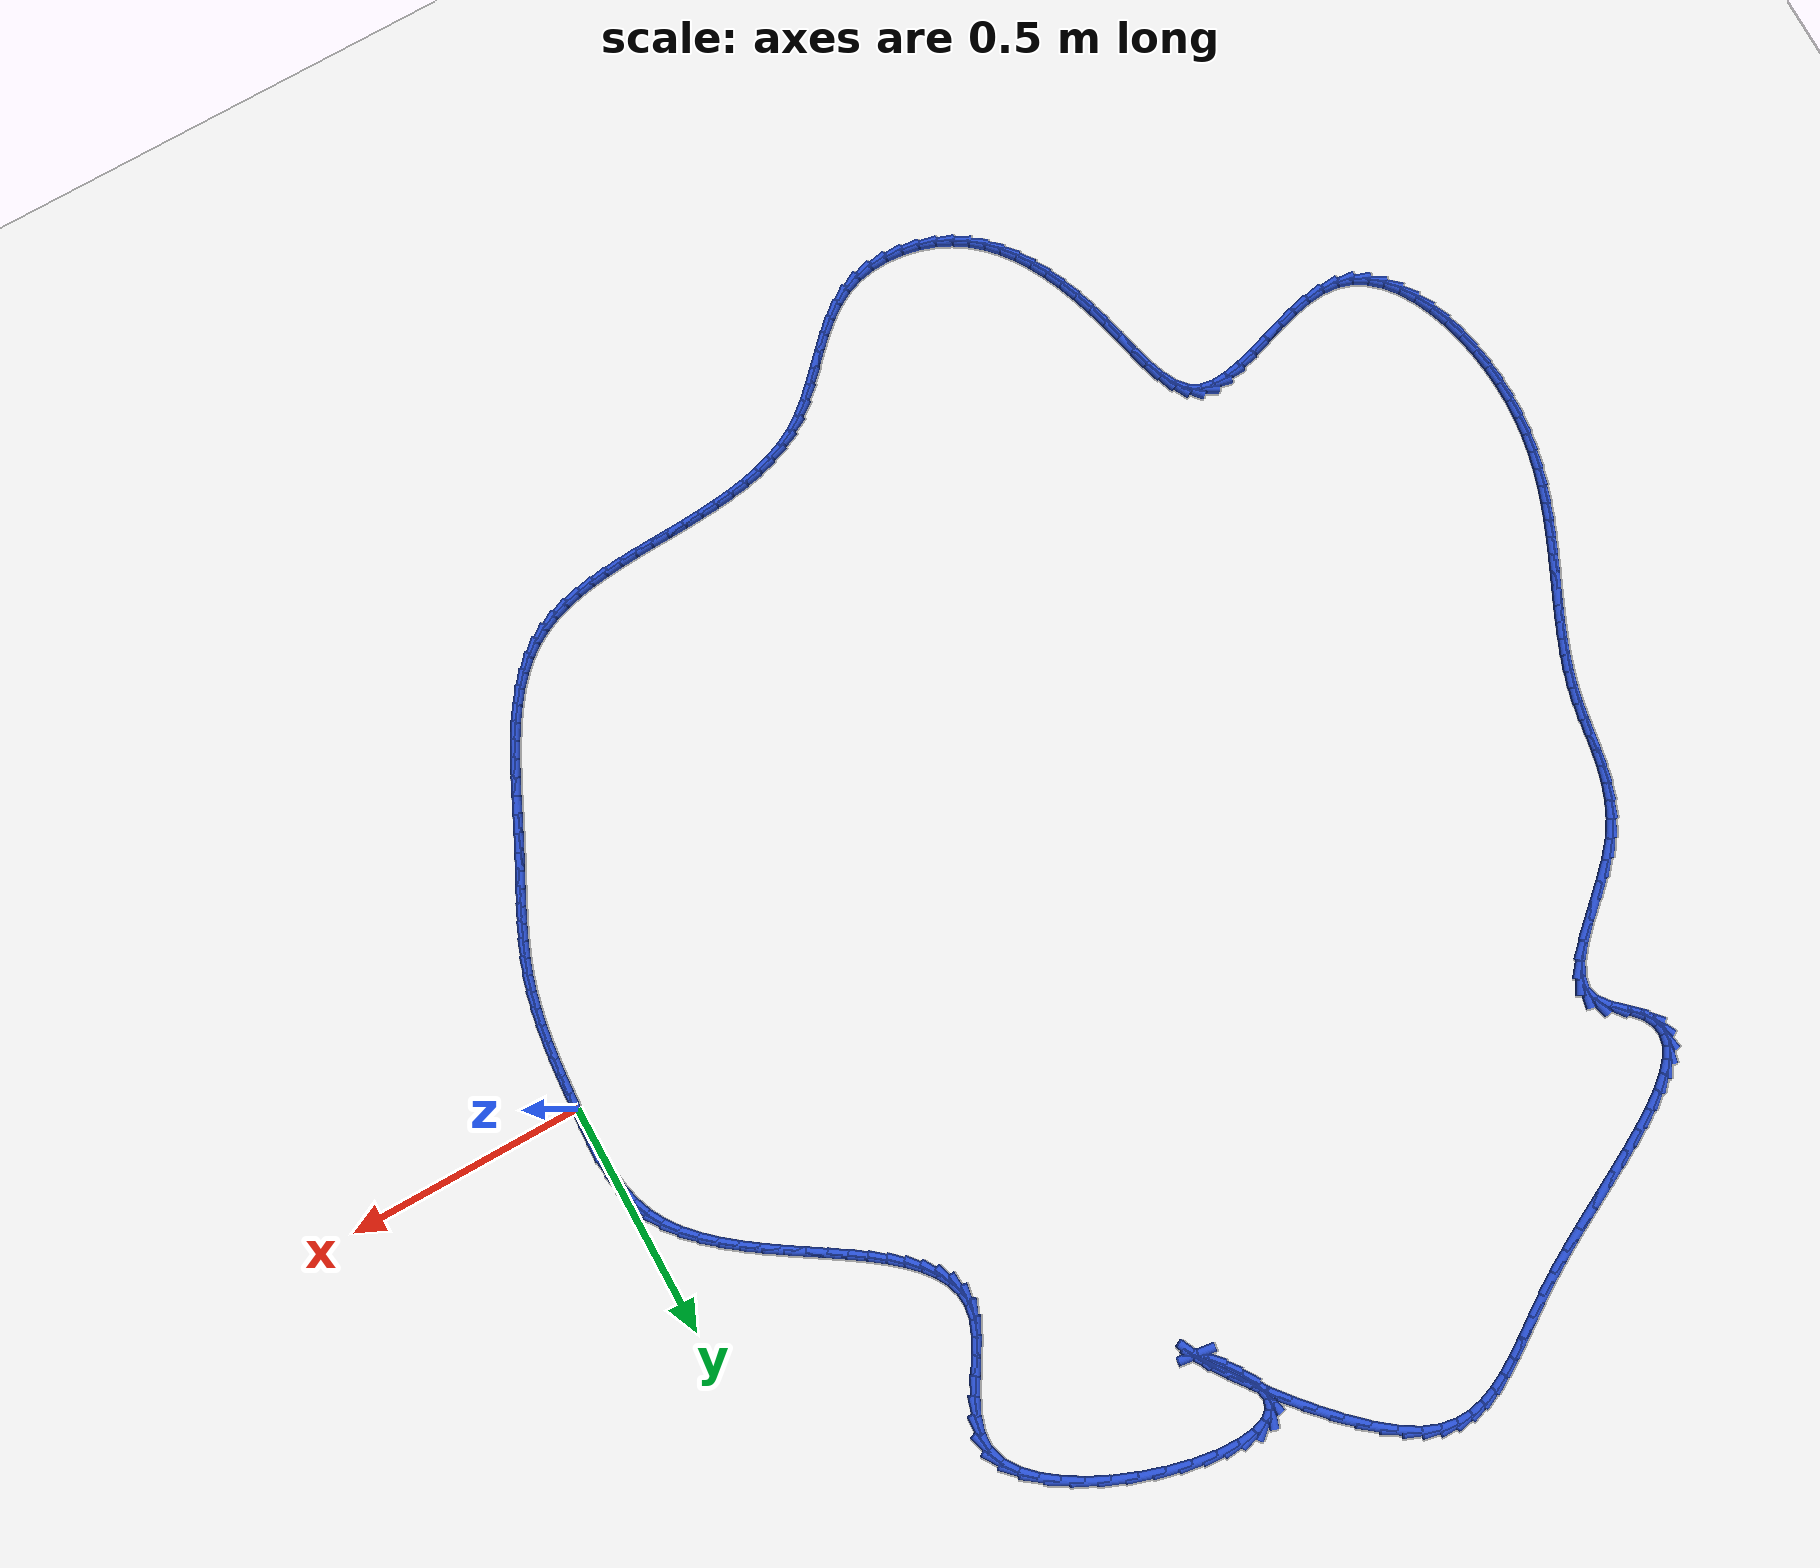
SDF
<sdf version="1.6">
 <world name="default">
  <light name="sun" type="directional">
   <pose>0 0 10 0 -0 0</pose>
   <diffuse>0.8 0.8 0.8 1</diffuse>
   <specular>0.2 0.2 0.2 1</specular>
   <attenuation>
    <range>1000</range>
    <constant>0.9</constant>
    <linear>0.01</linear>
    <quadratic>0.001</quadratic>
   </attenuation>
   <direction>-0.5 0.1 -0.9</direction>
  </light>
  <model name="ground_plane">
   <static>1</static>
   <link name="link">
    <collision name="collision">
     <geometry><plane><normal>0 0 1</normal><size>100 100</size></plane></geometry>
     <surface><friction><ode><mu>100</mu><mu2>50</mu2></ode></friction></surface>
    </collision>
    <visual name="visual">
     <cast_shadows>0</cast_shadows>
     <geometry><plane><normal>0 0 1</normal><size>100 100</size></plane></geometry>
     <material>
      <script><uri>file://media/materials/scripts/gazebo.material</uri><name>Gazebo/WhiteGlow</name></script>
     </material>
    </visual>
   </link>
  </model>
  <gravity>0 0 -9.8</gravity>
  <magnetic_field>6e-06 2.3e-05 -4.2e-05</magnetic_field>
  <atmosphere type="adiabatic"/>
  <physics name="default_physics" default="0" type="ode">
   <max_step_size>0.001</max_step_size>
   <real_time_factor>1</real_time_factor>
   <real_time_update_rate>1000</real_time_update_rate>
  </physics>
  <scene><ambient>0.4 0.4 0.4 1</ambient><background>0.7 0.7 0.7 1</background><shadows>1</shadows></scene>
  <spherical_coordinates>
   <surface_model>EARTH_WGS84</surface_model>
   <latitude_deg>0</latitude_deg>
   <longitude_deg>0</longitude_deg>
   <elevation>0</elevation>
   <heading_deg>0</heading_deg>
  </spherical_coordinates>
  <model name="line">
   <link name="link_0">
    <pose>2.5587171270657905e-17 0.0 0.01 0 1.57 1.520064185407944</pose>
    <collision name="collision">
     <geometry><cylinder><radius>0.01</radius><length>0.08</length></cylinder></geometry>
    </collision>
    <visual name="visual">
     <material>
      <script><name>Gazebo/Blue</name><uri>file://media/materials/scripts/gazebo.material</uri></script>
     </material>
     <geometry><cylinder><radius>0.01</radius><length>0.08</length></cylinder></geometry>
    </visual>
   </link>
   <link name="link_1">
    <pose>0.0018748048719254883 0.036923262417382044 0.01 0 1.57 1.5421365924903336</pose>
    <collision name="collision">
     <geometry><cylinder><radius>0.01</radius><length>0.08</length></cylinder></geometry>
    </collision>
    <visual name="visual">
     <material>
      <script><name>Gazebo/Blue</name><uri>file://media/materials/scripts/gazebo.material</uri></script>
     </material>
     <geometry><cylinder><radius>0.01</radius><length>0.08</length></cylinder></geometry>
    </visual>
   </link>
   <link name="link_2">
    <pose>0.002933559844912836 0.07385539394660441 0.01 0 1.57 -1.5598060839219594</pose>
    <collision name="collision">
     <geometry><cylinder><radius>0.01</radius><length>0.08</length></cylinder></geometry>
    </collision>
    <visual name="visual">
     <material>
      <script><name>Gazebo/Blue</name><uri>file://media/materials/scripts/gazebo.material</uri></script>
     </material>
     <geometry><cylinder><radius>0.01</radius><length>0.08</length></cylinder></geometry>
    </visual>
   </link>
   <link name="link_3">
    <pose>0.0025304025630716585 0.11053711741062097 0.01 0 1.57 -1.5014911245094156</pose>
    <collision name="collision">
     <geometry><cylinder><radius>0.01</radius><length>0.08</length></cylinder></geometry>
    </collision>
    <visual name="visual">
     <material>
      <script><name>Gazebo/Blue</name><uri>file://media/materials/scripts/gazebo.material</uri></script>
     </material>
     <geometry><cylinder><radius>0.01</radius><length>0.08</length></cylinder></geometry>
    </visual>
   </link>
   <link name="link_4">
    <pose>1.9470670511547924e-05 0.14670915563238576 0.01 0 1.57 -1.4231743809948845</pose>
    <collision name="collision">
     <geometry><cylinder><radius>0.01</radius><length>0.08</length></cylinder></geometry>
    </collision>
    <visual name="visual">
     <material>
      <script><name>Gazebo/Blue</name><uri>file://media/materials/scripts/gazebo.material</uri></script>
     </material>
     <geometry><cylinder><radius>0.01</radius><length>0.08</length></cylinder></geometry>
    </visual>
   </link>
   <link name="link_5">
    <pose>-0.0052450981886579 0.18211223143485256 0.01 0 1.57 -1.3238921737868379</pose>
    <collision name="collision">
     <geometry><cylinder><radius>0.01</radius><length>0.08</length></cylinder></geometry>
    </collision>
    <visual name="visual">
     <material>
      <script><name>Gazebo/Blue</name><uri>file://media/materials/scripts/gazebo.material</uri></script>
     </material>
     <geometry><cylinder><radius>0.01</radius><length>0.08</length></cylinder></geometry>
    </visual>
   </link>
   <link name="link_6">
    <pose>-0.013909166370327106 0.2164870676409754 0.01 0 1.57 -1.2040559883007989</pose>
    <collision name="collision">
     <geometry><cylinder><radius>0.01</radius><length>0.08</length></cylinder></geometry>
    </collision>
    <visual name="visual">
     <material>
      <script><name>Gazebo/Blue</name><uri>file://media/materials/scripts/gazebo.material</uri></script>
     </material>
     <geometry><cylinder><radius>0.01</radius><length>0.08</length></cylinder></geometry>
    </visual>
   </link>
   <link name="link_7">
    <pose>-0.026618596230386468 0.24957438707370808 0.01 0 1.57 -1.0669712356986034</pose>
    <collision name="collision">
     <geometry><cylinder><radius>0.01</radius><length>0.08</length></cylinder></geometry>
    </collision>
    <visual name="visual">
     <material>
      <script><name>Gazebo/Blue</name><uri>file://media/materials/scripts/gazebo.material</uri></script>
     </material>
     <geometry><cylinder><radius>0.01</radius><length>0.08</length></cylinder></geometry>
    </visual>
   </link>
   <link name="link_8">
    <pose>-0.04400820820827096 0.28111847519557936 0.01 0 1.57 -0.9330196016318371</pose>
    <collision name="collision">
     <geometry><cylinder><radius>0.01</radius><length>0.08</length></cylinder></geometry>
    </collision>
    <visual name="visual">
     <material>
      <script><name>Gazebo/Blue</name><uri>file://media/materials/scripts/gazebo.material</uri></script>
     </material>
     <geometry><cylinder><radius>0.01</radius><length>0.08</length></cylinder></geometry>
    </visual>
   </link>
   <link name="link_9">
    <pose>-0.06617963887287105 0.3110356475660228 0.01 0 1.57 -0.8247652183815631</pose>
    <collision name="collision">
     <geometry><cylinder><radius>0.01</radius><length>0.08</length></cylinder></geometry>
    </collision>
    <visual name="visual">
     <material>
      <script><name>Gazebo/Blue</name><uri>file://media/materials/scripts/gazebo.material</uri></script>
     </material>
     <geometry><cylinder><radius>0.01</radius><length>0.08</length></cylinder></geometry>
    </visual>
   </link>
   <link name="link_10">
    <pose>-0.0924749462323473 0.33948729537527816 0.01 0 1.57 -0.7408189495058372</pose>
    <collision name="collision">
     <geometry><cylinder><radius>0.01</radius><length>0.08</length></cylinder></geometry>
    </collision>
    <visual name="visual">
     <material>
      <script><name>Gazebo/Blue</name><uri>file://media/materials/scripts/gazebo.material</uri></script>
     </material>
     <geometry><cylinder><radius>0.01</radius><length>0.08</length></cylinder></geometry>
    </visual>
   </link>
   <link name="link_11">
    <pose>-0.12217808221640543 0.36665355755682955 0.01 0 1.57 -0.6774658057990955</pose>
    <collision name="collision">
     <geometry><cylinder><radius>0.01</radius><length>0.08</length></cylinder></geometry>
    </collision>
    <visual name="visual">
     <material>
      <script><name>Gazebo/Blue</name><uri>file://media/materials/scripts/gazebo.material</uri></script>
     </material>
     <geometry><cylinder><radius>0.01</radius><length>0.08</length></cylinder></geometry>
    </visual>
   </link>
   <link name="link_12">
    <pose>-0.1545729987547511 0.3927145730441617 0.01 0 1.57 -0.631437659492489</pose>
    <collision name="collision">
     <geometry><cylinder><radius>0.01</radius><length>0.08</length></cylinder></geometry>
    </collision>
    <visual name="visual">
     <material>
      <script><name>Gazebo/Blue</name><uri>file://media/materials/scripts/gazebo.material</uri></script>
     </material>
     <geometry><cylinder><radius>0.01</radius><length>0.08</length></cylinder></geometry>
    </visual>
   </link>
   <link name="link_13">
    <pose>-0.18894364777708997 0.417850480770759 0.01 0 1.57 -0.6002851134656657</pose>
    <collision name="collision">
     <geometry><cylinder><radius>0.01</radius><length>0.08</length></cylinder></geometry>
    </collision>
    <visual name="visual">
     <material>
      <script><name>Gazebo/Blue</name><uri>file://media/materials/scripts/gazebo.material</uri></script>
     </material>
     <geometry><cylinder><radius>0.01</radius><length>0.08</length></cylinder></geometry>
    </visual>
   </link>
   <link name="link_14">
    <pose>-0.22457398121312772 0.442241419670106 0.01 0 1.57 -0.5824344369787126</pose>
    <collision name="collision">
     <geometry><cylinder><radius>0.01</radius><length>0.08</length></cylinder></geometry>
    </collision>
    <visual name="visual">
     <material>
      <script><name>Gazebo/Blue</name><uri>file://media/materials/scripts/gazebo.material</uri></script>
     </material>
     <geometry><cylinder><radius>0.01</radius><length>0.08</length></cylinder></geometry>
    </visual>
   </link>
   <link name="link_15">
    <pose>-0.2607479509925701 0.46606752867568735 0.01 0 1.57 -0.5771637940019766</pose>
    <collision name="collision">
     <geometry><cylinder><radius>0.01</radius><length>0.08</length></cylinder></geometry>
    </collision>
    <visual name="visual">
     <material>
      <script><name>Gazebo/Blue</name><uri>file://media/materials/scripts/gazebo.material</uri></script>
     </material>
     <geometry><cylinder><radius>0.01</radius><length>0.08</length></cylinder></geometry>
    </visual>
   </link>
   <link name="link_16">
    <pose>-0.29674950904512276 0.48950894672098744 0.01 0 1.57 -0.5846063437951649</pose>
    <collision name="collision">
     <geometry><cylinder><radius>0.01</radius><length>0.08</length></cylinder></geometry>
    </collision>
    <visual name="visual">
     <material>
      <script><name>Gazebo/Blue</name><uri>file://media/materials/scripts/gazebo.material</uri></script>
     </material>
     <geometry><cylinder><radius>0.01</radius><length>0.08</length></cylinder></geometry>
    </visual>
   </link>
   <link name="link_17">
    <pose>-0.3318626073004915 0.5127458127394908 0.01 0 1.57 -0.6058310371188003</pose>
    <collision name="collision">
     <geometry><cylinder><radius>0.01</radius><length>0.08</length></cylinder></geometry>
    </collision>
    <visual name="visual">
     <material>
      <script><name>Gazebo/Blue</name><uri>file://media/materials/scripts/gazebo.material</uri></script>
     </material>
     <geometry><cylinder><radius>0.01</radius><length>0.08</length></cylinder></geometry>
    </visual>
   </link>
   <link name="link_18">
    <pose>-0.3653711976883818 0.535958265664682 0.01 0 1.57 -0.6430321062167901</pose>
    <collision name="collision">
     <geometry><cylinder><radius>0.01</radius><length>0.08</length></cylinder></geometry>
    </collision>
    <visual name="visual">
     <material>
      <script><name>Gazebo/Blue</name><uri>file://media/materials/scripts/gazebo.material</uri></script>
     </material>
     <geometry><cylinder><radius>0.01</radius><length>0.08</length></cylinder></geometry>
    </visual>
   </link>
   <link name="link_19">
    <pose>-0.3965592321384994 0.5593264444300454 0.01 0 1.57 -0.6998424838517474</pose>
    <collision name="collision">
     <geometry><cylinder><radius>0.01</radius><length>0.08</length></cylinder></geometry>
    </collision>
    <visual name="visual">
     <material>
      <script><name>Gazebo/Blue</name><uri>file://media/materials/scripts/gazebo.material</uri></script>
     </material>
     <geometry><cylinder><radius>0.01</radius><length>0.08</length></cylinder></geometry>
    </visual>
   </link>
   <link name="link_20">
    <pose>-0.42471066258055024 0.5830304879690658 0.01 0 1.57 -0.7817220089417507</pose>
    <collision name="collision">
     <geometry><cylinder><radius>0.01</radius><length>0.08</length></cylinder></geometry>
    </collision>
    <visual name="visual">
     <material>
      <script><name>Gazebo/Blue</name><uri>file://media/materials/scripts/gazebo.material</uri></script>
     </material>
     <geometry><cylinder><radius>0.01</radius><length>0.08</length></cylinder></geometry>
    </visual>
   </link>
   <link name="link_21">
    <pose>-0.4491094409442397 0.6072505352152273 0.01 0 1.57 -0.8961257143960141</pose>
    <collision name="collision">
     <geometry><cylinder><radius>0.01</radius><length>0.08</length></cylinder></geometry>
    </collision>
    <visual name="visual">
     <material>
      <script><name>Gazebo/Blue</name><uri>file://media/materials/scripts/gazebo.material</uri></script>
     </material>
     <geometry><cylinder><radius>0.01</radius><length>0.08</length></cylinder></geometry>
    </visual>
   </link>
   <link name="link_22">
    <pose>-0.46903951915927344 0.6321667251020147 0.01 0 1.57 -1.0514522231459567</pose>
    <collision name="collision">
     <geometry><cylinder><radius>0.01</radius><length>0.08</length></cylinder></geometry>
    </collision>
    <visual name="visual">
     <material>
      <script><name>Gazebo/Blue</name><uri>file://media/materials/scripts/gazebo.material</uri></script>
     </material>
     <geometry><cylinder><radius>0.01</radius><length>0.08</length></cylinder></geometry>
    </visual>
   </link>
   <link name="link_23">
    <pose>-0.48378484915535747 0.6579591965629125 0.01 0 1.57 -1.2525728478445552</pose>
    <collision name="collision">
     <geometry><cylinder><radius>0.01</radius><length>0.08</length></cylinder></geometry>
    </collision>
    <visual name="visual">
     <material>
      <script><name>Gazebo/Blue</name><uri>file://media/materials/scripts/gazebo.material</uri></script>
     </material>
     <geometry><cylinder><radius>0.01</radius><length>0.08</length></cylinder></geometry>
    </visual>
   </link>
   <link name="link_24">
    <pose>-0.49262938286219726 0.6848080885314052 0.01 0 1.57 -1.49164377486489</pose>
    <collision name="collision">
     <geometry><cylinder><radius>0.01</radius><length>0.08</length></cylinder></geometry>
    </collision>
    <visual name="visual">
     <material>
      <script><name>Gazebo/Blue</name><uri>file://media/materials/scripts/gazebo.material</uri></script>
     </material>
     <geometry><cylinder><radius>0.01</radius><length>0.08</length></cylinder></geometry>
    </visual>
   </link>
   <link name="link_25">
    <pose>-0.4948570722094984 0.712893539940977 0.01 0 1.57 1.399448730763973</pose>
    <collision name="collision">
     <geometry><cylinder><radius>0.01</radius><length>0.08</length></cylinder></geometry>
    </collision>
    <visual name="visual">
     <material>
      <script><name>Gazebo/Blue</name><uri>file://media/materials/scripts/gazebo.material</uri></script>
     </material>
     <geometry><cylinder><radius>0.01</radius><length>0.08</length></cylinder></geometry>
    </visual>
   </link>
   <link name="link_26">
    <pose>-0.48975188948038867 0.7423956867985229 0.01 0 1.57 1.1872710102072972</pose>
    <collision name="collision">
     <geometry><cylinder><radius>0.01</radius><length>0.08</length></cylinder></geometry>
    </collision>
    <visual name="visual">
     <material>
      <script><name>Gazebo/Blue</name><uri>file://media/materials/scripts/gazebo.material</uri></script>
     </material>
     <geometry><cylinder><radius>0.01</radius><length>0.08</length></cylinder></geometry>
    </visual>
   </link>
   <link name="link_27">
    <pose>-0.47724055016959666 0.7734022459600641 0.01 0 1.57 1.069986642342775</pose>
    <collision name="collision">
     <geometry><cylinder><radius>0.01</radius><length>0.08</length></cylinder></geometry>
    </collision>
    <visual name="visual">
     <material>
      <script><name>Gazebo/Blue</name><uri>file://media/materials/scripts/gazebo.material</uri></script>
     </material>
     <geometry><cylinder><radius>0.01</radius><length>0.08</length></cylinder></geometry>
    </visual>
   </link>
   <link name="link_28">
    <pose>-0.45958099337475516 0.8056657308878157 0.01 0 1.57 1.028091916802376</pose>
    <collision name="collision">
     <geometry><cylinder><radius>0.01</radius><length>0.08</length></cylinder></geometry>
    </collision>
    <visual name="visual">
     <material>
      <script><name>Gazebo/Blue</name><uri>file://media/materials/scripts/gazebo.material</uri></script>
     </material>
     <geometry><cylinder><radius>0.01</radius><length>0.08</length></cylinder></geometry>
    </visual>
   </link>
   <link name="link_29">
    <pose>-0.4395595219218643 0.8388626823596508 0.01 0 1.57 1.0454549955655694</pose>
    <collision name="collision">
     <geometry><cylinder><radius>0.01</radius><length>0.08</length></cylinder></geometry>
    </collision>
    <visual name="visual">
     <material>
      <script><name>Gazebo/Blue</name><uri>file://media/materials/scripts/gazebo.material</uri></script>
     </material>
     <geometry><cylinder><radius>0.01</radius><length>0.08</length></cylinder></geometry>
    </visual>
   </link>
   <link name="link_30">
    <pose>-0.4199624386369246 0.8726696411534444 0.01 0 1.57 1.122763732345513</pose>
    <collision name="collision">
     <geometry><cylinder><radius>0.01</radius><length>0.08</length></cylinder></geometry>
    </collision>
    <visual name="visual">
     <material>
      <script><name>Gazebo/Blue</name><uri>file://media/materials/scripts/gazebo.material</uri></script>
     </material>
     <geometry><cylinder><radius>0.01</radius><length>0.08</length></cylinder></geometry>
    </visual>
   </link>
   <link name="link_31">
    <pose>-0.4035760463459354 0.9067631480470685 0.01 0 1.57 1.2747013116488342</pose>
    <collision name="collision">
     <geometry><cylinder><radius>0.01</radius><length>0.08</length></cylinder></geometry>
    </collision>
    <visual name="visual">
     <material>
      <script><name>Gazebo/Blue</name><uri>file://media/materials/scripts/gazebo.material</uri></script>
     </material>
     <geometry><cylinder><radius>0.01</radius><length>0.08</length></cylinder></geometry>
    </visual>
   </link>
   <link name="link_32">
    <pose>-0.3931866478748973 0.9408197438183973 0.01 0 1.57 1.5231682267717563</pose>
    <collision name="collision">
     <geometry><cylinder><radius>0.01</radius><length>0.08</length></cylinder></geometry>
    </collision>
    <visual name="visual">
     <material>
      <script><name>Gazebo/Blue</name><uri>file://media/materials/scripts/gazebo.material</uri></script>
     </material>
     <geometry><cylinder><radius>0.01</radius><length>0.08</length></cylinder></geometry>
    </visual>
   </link>
   <link name="link_33">
    <pose>-0.39158054604981035 0.9745159692453044 0.01 0 1.57 -1.284390922418755</pose>
    <collision name="collision">
     <geometry><cylinder><radius>0.01</radius><length>0.08</length></cylinder></geometry>
    </collision>
    <visual name="visual">
     <material>
      <script><name>Gazebo/Blue</name><uri>file://media/materials/scripts/gazebo.material</uri></script>
     </material>
     <geometry><cylinder><radius>0.01</radius><length>0.08</length></cylinder></geometry>
    </visual>
   </link>
   <link name="link_34">
    <pose>-0.40130089121839285 1.0075219803329598 0.01 0 1.57 -0.9901545867470214</pose>
    <collision name="collision">
     <geometry><cylinder><radius>0.01</radius><length>0.08</length></cylinder></geometry>
    </collision>
    <visual name="visual">
     <material>
      <script><name>Gazebo/Blue</name><uri>file://media/materials/scripts/gazebo.material</uri></script>
     </material>
     <geometry><cylinder><radius>0.01</radius><length>0.08</length></cylinder></geometry>
    </visual>
   </link>
   <link name="link_35">
    <pose>-0.42224077379820546 1.0394383469962565 0.01 0 1.57 -0.7847639087961967</pose>
    <collision name="collision">
     <geometry><cylinder><radius>0.01</radius><length>0.08</length></cylinder></geometry>
    </collision>
    <visual name="visual">
     <material>
      <script><name>Gazebo/Blue</name><uri>file://media/materials/scripts/gazebo.material</uri></script>
     </material>
     <geometry><cylinder><radius>0.01</radius><length>0.08</length></cylinder></geometry>
    </visual>
   </link>
   <link name="link_36">
    <pose>-0.45266384718471 1.0698228528906395 0.01 0 1.57 -0.6401403869923044</pose>
    <collision name="collision">
     <geometry><cylinder><radius>0.01</radius><length>0.08</length></cylinder></geometry>
    </collision>
    <visual name="visual">
     <material>
      <script><name>Gazebo/Blue</name><uri>file://media/materials/scripts/gazebo.material</uri></script>
     </material>
     <geometry><cylinder><radius>0.01</radius><length>0.08</length></cylinder></geometry>
    </visual>
   </link>
   <link name="link_37">
    <pose>-0.49080999665978603 1.098232657561105 0.01 0 1.57 -0.5324939024317938</pose>
    <collision name="collision">
     <geometry><cylinder><radius>0.01</radius><length>0.08</length></cylinder></geometry>
    </collision>
    <visual name="visual">
     <material>
      <script><name>Gazebo/Blue</name><uri>file://media/materials/scripts/gazebo.material</uri></script>
     </material>
     <geometry><cylinder><radius>0.01</radius><length>0.08</length></cylinder></geometry>
    </visual>
   </link>
   <link name="link_38">
    <pose>-0.5349191075053128 1.1242249205526478 0.01 0 1.57 -0.44654617275749103</pose>
    <collision name="collision">
     <geometry><cylinder><radius>0.01</radius><length>0.08</length></cylinder></geometry>
    </collision>
    <visual name="visual">
     <material>
      <script><name>Gazebo/Blue</name><uri>file://media/materials/scripts/gazebo.material</uri></script>
     </material>
     <geometry><cylinder><radius>0.01</radius><length>0.08</length></cylinder></geometry>
    </visual>
   </link>
   <link name="link_39">
    <pose>-0.5832310650031705 1.1473568014102635 0.01 0 1.57 -0.3724430227063726</pose>
    <collision name="collision">
     <geometry><cylinder><radius>0.01</radius><length>0.08</length></cylinder></geometry>
    </collision>
    <visual name="visual">
     <material>
      <script><name>Gazebo/Blue</name><uri>file://media/materials/scripts/gazebo.material</uri></script>
     </material>
     <geometry><cylinder><radius>0.01</radius><length>0.08</length></cylinder></geometry>
    </visual>
   </link>
   <link name="link_40">
    <pose>-0.6339857544352379 1.1671854596789475 0.01 0 1.57 -0.30303429152915823</pose>
    <collision name="collision">
     <geometry><cylinder><radius>0.01</radius><length>0.08</length></cylinder></geometry>
    </collision>
    <visual name="visual">
     <material>
      <script><name>Gazebo/Blue</name><uri>file://media/materials/scripts/gazebo.material</uri></script>
     </material>
     <geometry><cylinder><radius>0.01</radius><length>0.08</length></cylinder></geometry>
    </visual>
   </link>
   <link name="link_41">
    <pose>-0.6854230610833948 1.1832680549036947 0.01 0 1.57 -0.23192449440451152</pose>
    <collision name="collision">
     <geometry><cylinder><radius>0.01</radius><length>0.08</length></cylinder></geometry>
    </collision>
    <visual name="visual">
     <material>
      <script><name>Gazebo/Blue</name><uri>file://media/materials/scripts/gazebo.material</uri></script>
     </material>
     <geometry><cylinder><radius>0.01</radius><length>0.08</length></cylinder></geometry>
    </visual>
   </link>
   <link name="link_42">
    <pose>-0.7357828702295204 1.1951617466295004 0.01 0 1.57 -0.15163863724956916</pose>
    <collision name="collision">
     <geometry><cylinder><radius>0.01</radius><length>0.08</length></cylinder></geometry>
    </collision>
    <visual name="visual">
     <material>
      <script><name>Gazebo/Blue</name><uri>file://media/materials/scripts/gazebo.material</uri></script>
     </material>
     <geometry><cylinder><radius>0.01</radius><length>0.08</length></cylinder></geometry>
    </visual>
   </link>
   <link name="link_43">
    <pose>-0.7833050671554944 1.20242369440136 0.01 0 1.57 -0.050914384143007446</pose>
    <collision name="collision">
     <geometry><cylinder><radius>0.01</radius><length>0.08</length></cylinder></geometry>
    </collision>
    <visual name="visual">
     <material>
      <script><name>Gazebo/Blue</name><uri>file://media/materials/scripts/gazebo.material</uri></script>
     </material>
     <geometry><cylinder><radius>0.01</radius><length>0.08</length></cylinder></geometry>
    </visual>
   </link>
   <link name="link_44">
    <pose>-0.8262295371431961 1.2046110577642688 0.01 0 1.57 0.09081781133068623</pose>
    <collision name="collision">
     <geometry><cylinder><radius>0.01</radius><length>0.08</length></cylinder></geometry>
    </collision>
    <visual name="visual">
     <material>
      <script><name>Gazebo/Blue</name><uri>file://media/materials/scripts/gazebo.material</uri></script>
     </material>
     <geometry><cylinder><radius>0.01</radius><length>0.08</length></cylinder></geometry>
    </visual>
   </link>
   <link name="link_45">
    <pose>-0.8627961654745052 1.2012809962632223 0.01 0 1.57 0.3156462998889674</pose>
    <collision name="collision">
     <geometry><cylinder><radius>0.01</radius><length>0.08</length></cylinder></geometry>
    </collision>
    <visual name="visual">
     <material>
      <script><name>Gazebo/Blue</name><uri>file://media/materials/scripts/gazebo.material</uri></script>
     </material>
     <geometry><cylinder><radius>0.01</radius><length>0.08</length></cylinder></geometry>
    </visual>
   </link>
   <link name="link_46">
    <pose>-0.8912448374313007 1.1919906694432152 0.01 0 1.57 0.7016241853373001</pose>
    <collision name="collision">
     <geometry><cylinder><radius>0.01</radius><length>0.08</length></cylinder></geometry>
    </collision>
    <visual name="visual">
     <material>
      <script><name>Gazebo/Blue</name><uri>file://media/materials/scripts/gazebo.material</uri></script>
     </material>
     <geometry><cylinder><radius>0.01</radius><length>0.08</length></cylinder></geometry>
    </visual>
   </link>
   <link name="link_47">
    <pose>-0.9098154382954626 1.1762972368492433 0.01 0 1.57 1.2724100079755536</pose>
    <collision name="collision">
     <geometry><cylinder><radius>0.01</radius><length>0.08</length></cylinder></geometry>
    </collision>
    <visual name="visual">
     <material>
      <script><name>Gazebo/Blue</name><uri>file://media/materials/scripts/gazebo.material</uri></script>
     </material>
     <geometry><cylinder><radius>0.01</radius><length>0.08</length></cylinder></geometry>
    </visual>
   </link>
   <link name="link_48">
    <pose>-0.9167478533488701 1.1537578580263017 0.01 0 1.57 -1.3605881898114365</pose>
    <collision name="collision">
     <geometry><cylinder><radius>0.01</radius><length>0.08</length></cylinder></geometry>
    </collision>
    <visual name="visual">
     <material>
      <script><name>Gazebo/Blue</name><uri>file://media/materials/scripts/gazebo.material</uri></script>
     </material>
     <geometry><cylinder><radius>0.01</radius><length>0.08</length></cylinder></geometry>
    </visual>
   </link>
   <link name="link_49">
    <pose>-0.9104036037454868 1.124022911377311 0.01 0 1.57 -1.0990846913617078</pose>
    <collision name="collision">
     <geometry><cylinder><radius>0.01</radius><length>0.08</length></cylinder></geometry>
    </collision>
    <visual name="visual">
     <material>
      <script><name>Gazebo/Blue</name><uri>file://media/materials/scripts/gazebo.material</uri></script>
     </material>
     <geometry><cylinder><radius>0.01</radius><length>0.08</length></cylinder></geometry>
    </visual>
   </link>
   <link name="link_50">
    <pose>-0.8928253388496156 1.0895639049749528 0.01 0 1.57 -0.9783363518609454</pose>
    <collision name="collision">
     <geometry><cylinder><radius>0.01</radius><length>0.08</length></cylinder></geometry>
    </collision>
    <visual name="visual">
     <material>
      <script><name>Gazebo/Blue</name><uri>file://media/materials/scripts/gazebo.material</uri></script>
     </material>
     <geometry><cylinder><radius>0.01</radius><length>0.08</length></cylinder></geometry>
    </visual>
   </link>
   <link name="link_51">
    <pose>-0.8703069908177976 1.0561104295596215 0.01 0 1.57 -0.903025063780244</pose>
    <collision name="collision">
     <geometry><cylinder><radius>0.01</radius><length>0.08</length></cylinder></geometry>
    </collision>
    <visual name="visual">
     <material>
      <script><name>Gazebo/Blue</name><uri>file://media/materials/scripts/gazebo.material</uri></script>
     </material>
     <geometry><cylinder><radius>0.01</radius><length>0.08</length></cylinder></geometry>
    </visual>
   </link>
   <link name="link_52">
    <pose>-0.8493789003561748 1.0295732537974323 0.01 0 1.57 -0.8190433403129486</pose>
    <collision name="collision">
     <geometry><cylinder><radius>0.01</radius><length>0.08</length></cylinder></geometry>
    </collision>
    <visual name="visual">
     <material>
      <script><name>Gazebo/Blue</name><uri>file://media/materials/scripts/gazebo.material</uri></script>
     </material>
     <geometry><cylinder><radius>0.01</radius><length>0.08</length></cylinder></geometry>
    </visual>
   </link>
   <link name="link_53">
    <pose>-0.8362303111858819 1.0155087289531846 0.01 0 1.57 -0.13340953950688866</pose>
    <collision name="collision">
     <geometry><cylinder><radius>0.01</radius><length>0.08</length></cylinder></geometry>
    </collision>
    <visual name="visual">
     <material>
      <script><name>Gazebo/Blue</name><uri>file://media/materials/scripts/gazebo.material</uri></script>
     </material>
     <geometry><cylinder><radius>0.01</radius><length>0.08</length></cylinder></geometry>
    </visual>
   </link>
   <link name="link_54">
    <pose>-0.83279072428813 1.0150471133664551 0.01 0 1.57 -1.1306974412197297</pose>
    <collision name="collision">
     <geometry><cylinder><radius>0.01</radius><length>0.08</length></cylinder></geometry>
    </collision>
    <visual name="visual">
     <material>
      <script><name>Gazebo/Blue</name><uri>file://media/materials/scripts/gazebo.material</uri></script>
     </material>
     <geometry><cylinder><radius>0.01</radius><length>0.08</length></cylinder></geometry>
    </visual>
   </link>
   <link name="link_55">
    <pose>-0.8380947964665578 1.0263107726198504 0.01 0 1.57 -1.0167029874155322</pose>
    <collision name="collision">
     <geometry><cylinder><radius>0.01</radius><length>0.08</length></cylinder></geometry>
    </collision>
    <visual name="visual">
     <material>
      <script><name>Gazebo/Blue</name><uri>file://media/materials/scripts/gazebo.material</uri></script>
     </material>
     <geometry><cylinder><radius>0.01</radius><length>0.08</length></cylinder></geometry>
    </visual>
   </link>
   <link name="link_56">
    <pose>-0.8511219004037264 1.0473646292361183 0.01 0 1.57 -0.9719326227896494</pose>
    <collision name="collision">
     <geometry><cylinder><radius>0.01</radius><length>0.08</length></cylinder></geometry>
    </collision>
    <visual name="visual">
     <material>
      <script><name>Gazebo/Blue</name><uri>file://media/materials/scripts/gazebo.material</uri></script>
     </material>
     <geometry><cylinder><radius>0.01</radius><length>0.08</length></cylinder></geometry>
    </visual>
   </link>
   <link name="link_57">
    <pose>-0.8708514087821955 1.076273605738009 0.01 0 1.57 -0.9404789385424247</pose>
    <collision name="collision">
     <geometry><cylinder><radius>0.01</radius><length>0.08</length></cylinder></geometry>
    </collision>
    <visual name="visual">
     <material>
      <script><name>Gazebo/Blue</name><uri>file://media/materials/scripts/gazebo.material</uri></script>
     </material>
     <geometry><cylinder><radius>0.01</radius><length>0.08</length></cylinder></geometry>
    </visual>
   </link>
   <link name="link_58">
    <pose>-0.8962626942845251 1.1111026246482705 0.01 0 1.57 -0.9116215152533304</pose>
    <collision name="collision">
     <geometry><cylinder><radius>0.01</radius><length>0.08</length></cylinder></geometry>
    </collision>
    <visual name="visual">
     <material>
      <script><name>Gazebo/Blue</name><uri>file://media/materials/scripts/gazebo.material</uri></script>
     </material>
     <geometry><cylinder><radius>0.01</radius><length>0.08</length></cylinder></geometry>
    </visual>
   </link>
   <link name="link_59">
    <pose>-0.9263351295932759 1.1499166084896524 0.01 0 1.57 -0.8809924382866111</pose>
    <collision name="collision">
     <geometry><cylinder><radius>0.01</radius><length>0.08</length></cylinder></geometry>
    </collision>
    <visual name="visual">
     <material>
      <script><name>Gazebo/Blue</name><uri>file://media/materials/scripts/gazebo.material</uri></script>
     </material>
     <geometry><cylinder><radius>0.01</radius><length>0.08</length></cylinder></geometry>
    </visual>
   </link>
   <link name="link_60">
    <pose>-0.9600480873910072 1.1907804797849026 0.01 0 1.57 -0.8454182919945205</pose>
    <collision name="collision">
     <geometry><cylinder><radius>0.01</radius><length>0.08</length></cylinder></geometry>
    </collision>
    <visual name="visual">
     <material>
      <script><name>Gazebo/Blue</name><uri>file://media/materials/scripts/gazebo.material</uri></script>
     </material>
     <geometry><cylinder><radius>0.01</radius><length>0.08</length></cylinder></geometry>
    </visual>
   </link>
   <link name="link_61">
    <pose>-0.9963809403602805 1.2317591610567717 0.01 0 1.57 -0.8013040010850668</pose>
    <collision name="collision">
     <geometry><cylinder><radius>0.01</radius><length>0.08</length></cylinder></geometry>
    </collision>
    <visual name="visual">
     <material>
      <script><name>Gazebo/Blue</name><uri>file://media/materials/scripts/gazebo.material</uri></script>
     </material>
     <geometry><cylinder><radius>0.01</radius><length>0.08</length></cylinder></geometry>
    </visual>
   </link>
   <link name="link_62">
    <pose>-1.0343130611836548 1.270917574828007 0.01 0 1.57 -0.7433781073934148</pose>
    <collision name="collision">
     <geometry><cylinder><radius>0.01</radius><length>0.08</length></cylinder></geometry>
    </collision>
    <visual name="visual">
     <material>
      <script><name>Gazebo/Blue</name><uri>file://media/materials/scripts/gazebo.material</uri></script>
     </material>
     <geometry><cylinder><radius>0.01</radius><length>0.08</length></cylinder></geometry>
    </visual>
   </link>
   <link name="link_63">
    <pose>-1.072823822543691 1.3063206436213581 0.01 0 1.57 -0.6627365604325098</pose>
    <collision name="collision">
     <geometry><cylinder><radius>0.01</radius><length>0.08</length></cylinder></geometry>
    </collision>
    <visual name="visual">
     <material>
      <script><name>Gazebo/Blue</name><uri>file://media/materials/scripts/gazebo.material</uri></script>
     </material>
     <geometry><cylinder><radius>0.01</radius><length>0.08</length></cylinder></geometry>
    </visual>
   </link>
   <link name="link_64">
    <pose>-1.1108925971229486 1.3360332899595744 0.01 0 1.57 -0.5434095359581331</pose>
    <collision name="collision">
     <geometry><cylinder><radius>0.01</radius><length>0.08</length></cylinder></geometry>
    </collision>
    <visual name="visual">
     <material>
      <script><name>Gazebo/Blue</name><uri>file://media/materials/scripts/gazebo.material</uri></script>
     </material>
     <geometry><cylinder><radius>0.01</radius><length>0.08</length></cylinder></geometry>
    </visual>
   </link>
   <link name="link_65">
    <pose>-1.1475184767681623 1.3581580231236203 0.01 0 1.57 -0.3784171484410555</pose>
    <collision name="collision">
     <geometry><cylinder><radius>0.01</radius><length>0.08</length></cylinder></geometry>
    </collision>
    <visual name="visual">
     <material>
      <script><name>Gazebo/Blue</name><uri>file://media/materials/scripts/gazebo.material</uri></script>
     </material>
     <geometry><cylinder><radius>0.01</radius><length>0.08</length></cylinder></geometry>
    </visual>
   </link>
   <link name="link_66">
    <pose>-1.182330791656989 1.3719986515750053 0.01 0 1.57 -0.18613815783827042</pose>
    <collision name="collision">
     <geometry><cylinder><radius>0.01</radius><length>0.08</length></cylinder></geometry>
    </collision>
    <visual name="visual">
     <material>
      <script><name>Gazebo/Blue</name><uri>file://media/materials/scripts/gazebo.material</uri></script>
     </material>
     <geometry><cylinder><radius>0.01</radius><length>0.08</length></cylinder></geometry>
    </visual>
   </link>
   <link name="link_67">
    <pose>-1.2157064197040677 1.3782838867679512 0.01 0 1.57 0.014175235118178298</pose>
    <collision name="collision">
     <geometry><cylinder><radius>0.01</radius><length>0.08</length></cylinder></geometry>
    </collision>
    <visual name="visual">
     <material>
      <script><name>Gazebo/Blue</name><uri>file://media/materials/scripts/gazebo.material</uri></script>
     </material>
     <geometry><cylinder><radius>0.01</radius><length>0.08</length></cylinder></geometry>
    </visual>
   </link>
   <link name="link_68">
    <pose>-1.248065634384868 1.377825156565865 0.01 0 1.57 0.19856539048404523</pose>
    <collision name="collision">
     <geometry><cylinder><radius>0.01</radius><length>0.08</length></cylinder></geometry>
    </collision>
    <visual name="visual">
     <material>
      <script><name>Gazebo/Blue</name><uri>file://media/materials/scripts/gazebo.material</uri></script>
     </material>
     <geometry><cylinder><radius>0.01</radius><length>0.08</length></cylinder></geometry>
    </visual>
   </link>
   <link name="link_69">
    <pose>-1.2798287091748588 1.371433888832153 0.01 0 1.57 0.3495011470274727</pose>
    <collision name="collision">
     <geometry><cylinder><radius>0.01</radius><length>0.08</length></cylinder></geometry>
    </collision>
    <visual name="visual">
     <material>
      <script><name>Gazebo/Blue</name><uri>file://media/materials/scripts/gazebo.material</uri></script>
     </material>
     <geometry><cylinder><radius>0.01</radius><length>0.08</length></cylinder></geometry>
    </visual>
   </link>
   <link name="link_70">
    <pose>-1.3114159175495104 1.3599215114302228 0.01 0 1.57 0.4612887238114414</pose>
    <collision name="collision">
     <geometry><cylinder><radius>0.01</radius><length>0.08</length></cylinder></geometry>
    </collision>
    <visual name="visual">
     <material>
      <script><name>Gazebo/Blue</name><uri>file://media/materials/scripts/gazebo.material</uri></script>
     </material>
     <geometry><cylinder><radius>0.01</radius><length>0.08</length></cylinder></geometry>
    </visual>
   </link>
   <link name="link_71">
    <pose>-1.3432475329842921 1.3440994522234815 0.01 0 1.57 0.5363943340565612</pose>
    <collision name="collision">
     <geometry><cylinder><radius>0.01</radius><length>0.08</length></cylinder></geometry>
    </collision>
    <visual name="visual">
     <material>
      <script><name>Gazebo/Blue</name><uri>file://media/materials/scripts/gazebo.material</uri></script>
     </material>
     <geometry><cylinder><radius>0.01</radius><length>0.08</length></cylinder></geometry>
    </visual>
   </link>
   <link name="link_72">
    <pose>-1.3757438289546742 1.3247791390753352 0.01 0 1.57 0.580120079423631</pose>
    <collision name="collision">
     <geometry><cylinder><radius>0.01</radius><length>0.08</length></cylinder></geometry>
    </collision>
    <visual name="visual">
     <material>
      <script><name>Gazebo/Blue</name><uri>file://media/materials/scripts/gazebo.material</uri></script>
     </material>
     <geometry><cylinder><radius>0.01</radius><length>0.08</length></cylinder></geometry>
    </visual>
   </link>
   <link name="link_73">
    <pose>-1.4093250789361251 1.3027719998491927 0.01 0 1.57 0.5976390452263526</pose>
    <collision name="collision">
     <geometry><cylinder><radius>0.01</radius><length>0.08</length></cylinder></geometry>
    </collision>
    <visual name="visual">
     <material>
      <script><name>Gazebo/Blue</name><uri>file://media/materials/scripts/gazebo.material</uri></script>
     </material>
     <geometry><cylinder><radius>0.01</radius><length>0.08</length></cylinder></geometry>
    </visual>
   </link>
   <link name="link_74">
    <pose>-1.4444115564041156 1.2788894624084588 0.01 0 1.57 0.5930704271386178</pose>
    <collision name="collision">
     <geometry><cylinder><radius>0.01</radius><length>0.08</length></cylinder></geometry>
    </collision>
    <visual name="visual">
     <material>
      <script><name>Gazebo/Blue</name><uri>file://media/materials/scripts/gazebo.material</uri></script>
     </material>
     <geometry><cylinder><radius>0.01</radius><length>0.08</length></cylinder></geometry>
    </visual>
   </link>
   <link name="link_75">
    <pose>-1.481423534834114 1.253942954616542 0.01 0 1.57 0.5694950135395905</pose>
    <collision name="collision">
     <geometry><cylinder><radius>0.01</radius><length>0.08</length></cylinder></geometry>
    </collision>
    <visual name="visual">
     <material>
      <script><name>Gazebo/Blue</name><uri>file://media/materials/scripts/gazebo.material</uri></script>
     </material>
     <geometry><cylinder><radius>0.01</radius><length>0.08</length></cylinder></geometry>
    </visual>
   </link>
   <link name="link_76">
    <pose>-1.520781287701591 1.2287439043368489 0.01 0 1.57 0.5334228590717697</pose>
    <collision name="collision">
     <geometry><cylinder><radius>0.01</radius><length>0.08</length></cylinder></geometry>
    </collision>
    <visual name="visual">
     <material>
      <script><name>Gazebo/Blue</name><uri>file://media/materials/scripts/gazebo.material</uri></script>
     </material>
     <geometry><cylinder><radius>0.01</radius><length>0.08</length></cylinder></geometry>
    </visual>
   </link>
   <link name="link_77">
    <pose>-1.5627193597903268 1.2039784581757458 0.01 0 1.57 0.5046314881949909</pose>
    <collision name="collision">
     <geometry><cylinder><radius>0.01</radius><length>0.08</length></cylinder></geometry>
    </collision>
    <visual name="visual">
     <material>
      <script><name>Gazebo/Blue</name><uri>file://media/materials/scripts/gazebo.material</uri></script>
     </material>
     <geometry><cylinder><radius>0.01</radius><length>0.08</length></cylinder></geometry>
    </visual>
   </link>
   <link name="link_78">
    <pose>-1.6065979069327492 1.179742953238595 0.01 0 1.57 0.48690536730247236</pose>
    <collision name="collision">
     <geometry><cylinder><radius>0.01</radius><length>0.08</length></cylinder></geometry>
    </collision>
    <visual name="visual">
     <material>
      <script><name>Gazebo/Blue</name><uri>file://media/materials/scripts/gazebo.material</uri></script>
     </material>
     <geometry><cylinder><radius>0.01</radius><length>0.08</length></cylinder></geometry>
    </visual>
   </link>
   <link name="link_79">
    <pose>-1.6515200025091874 1.155960314475268 0.01 0 1.57 0.47901538798728127</pose>
    <collision name="collision">
     <geometry><cylinder><radius>0.01</radius><length>0.08</length></cylinder></geometry>
    </collision>
    <visual name="visual">
     <material>
      <script><name>Gazebo/Blue</name><uri>file://media/materials/scripts/gazebo.material</uri></script>
     </material>
     <geometry><cylinder><radius>0.01</radius><length>0.08</length></cylinder></geometry>
    </visual>
   </link>
   <link name="link_80">
    <pose>-1.6965886849014034 1.1325534432277389 0.01 0 1.57 0.48063197314140077</pose>
    <collision name="collision">
     <geometry><cylinder><radius>0.01</radius><length>0.08</length></cylinder></geometry>
    </collision>
    <visual name="visual">
     <material>
      <script><name>Gazebo/Blue</name><uri>file://media/materials/scripts/gazebo.material</uri></script>
     </material>
     <geometry><cylinder><radius>0.01</radius><length>0.08</length></cylinder></geometry>
    </visual>
   </link>
   <link name="link_81">
    <pose>-1.7409069924911624 1.1094452408379794 0.01 0 1.57 0.49230403348566804</pose>
    <collision name="collision">
     <geometry><cylinder><radius>0.01</radius><length>0.08</length></cylinder></geometry>
    </collision>
    <visual name="visual">
     <material>
      <script><name>Gazebo/Blue</name><uri>file://media/materials/scripts/gazebo.material</uri></script>
     </material>
     <geometry><cylinder><radius>0.01</radius><length>0.08</length></cylinder></geometry>
    </visual>
   </link>
   <link name="link_82">
    <pose>-1.783577963660225 1.0865586086479626 0.01 0 1.57 0.5156190370436068</pose>
    <collision name="collision">
     <geometry><cylinder><radius>0.01</radius><length>0.08</length></cylinder></geometry>
    </collision>
    <visual name="visual">
     <material>
      <script><name>Gazebo/Blue</name><uri>file://media/materials/scripts/gazebo.material</uri></script>
     </material>
     <geometry><cylinder><radius>0.01</radius><length>0.08</length></cylinder></geometry>
    </visual>
   </link>
   <link name="link_83">
    <pose>-1.823704636790356 1.063816447999661 0.01 0 1.57 0.553612926504866</pose>
    <collision name="collision">
     <geometry><cylinder><radius>0.01</radius><length>0.08</length></cylinder></geometry>
    </collision>
    <visual name="visual">
     <material>
      <script><name>Gazebo/Blue</name><uri>file://media/materials/scripts/gazebo.material</uri></script>
     </material>
     <geometry><cylinder><radius>0.01</radius><length>0.08</length></cylinder></geometry>
    </visual>
   </link>
   <link name="link_84">
    <pose>-1.8603900502633177 1.0411416602350483 0.01 0 1.57 0.6115860541325643</pose>
    <collision name="collision">
     <geometry><cylinder><radius>0.01</radius><length>0.08</length></cylinder></geometry>
    </collision>
    <visual name="visual">
     <material>
      <script><name>Gazebo/Blue</name><uri>file://media/materials/scripts/gazebo.material</uri></script>
     </material>
     <geometry><cylinder><radius>0.01</radius><length>0.08</length></cylinder></geometry>
    </visual>
   </link>
   <link name="link_85">
    <pose>-1.8927372424608733 1.0184571466960963 0.01 0 1.57 0.6986003556916734</pose>
    <collision name="collision">
     <geometry><cylinder><radius>0.01</radius><length>0.08</length></cylinder></geometry>
    </collision>
    <visual name="visual">
     <material>
      <script><name>Gazebo/Blue</name><uri>file://media/materials/scripts/gazebo.material</uri></script>
     </material>
     <geometry><cylinder><radius>0.01</radius><length>0.08</length></cylinder></geometry>
    </visual>
   </link>
   <link name="link_86">
    <pose>-1.9198492517647852 0.9956858087247785 0.01 0 1.57 0.8298954861789504</pose>
    <collision name="collision">
     <geometry><cylinder><radius>0.01</radius><length>0.08</length></cylinder></geometry>
    </collision>
    <visual name="visual">
     <material>
      <script><name>Gazebo/Blue</name><uri>file://media/materials/scripts/gazebo.material</uri></script>
     </material>
     <geometry><cylinder><radius>0.01</radius><length>0.08</length></cylinder></geometry>
    </visual>
   </link>
   <link name="link_87">
    <pose>-1.940829116556817 0.9727505476630675 0.01 0 1.57 1.028950722014643</pose>
    <collision name="collision">
     <geometry><cylinder><radius>0.01</radius><length>0.08</length></cylinder></geometry>
    </collision>
    <visual name="visual">
     <material>
      <script><name>Gazebo/Blue</name><uri>file://media/materials/scripts/gazebo.material</uri></script>
     </material>
     <geometry><cylinder><radius>0.01</radius><length>0.08</length></cylinder></geometry>
    </visual>
   </link>
   <link name="link_88">
    <pose>-1.9547798752187329 0.9495742648529355 0.01 0 1.57 1.3197742720940036</pose>
    <collision name="collision">
     <geometry><cylinder><radius>0.01</radius><length>0.08</length></cylinder></geometry>
    </collision>
    <visual name="visual">
     <material>
      <script><name>Gazebo/Blue</name><uri>file://media/materials/scripts/gazebo.material</uri></script>
     </material>
     <geometry><cylinder><radius>0.01</radius><length>0.08</length></cylinder></geometry>
    </visual>
   </link>
   <link name="link_89">
    <pose>-1.9608045661322941 0.9260798616363562 0.01 0 1.57 -1.4541915429639214</pose>
    <collision name="collision">
     <geometry><cylinder><radius>0.01</radius><length>0.08</length></cylinder></geometry>
    </collision>
    <visual name="visual">
     <material>
      <script><name>Gazebo/Blue</name><uri>file://media/materials/scripts/gazebo.material</uri></script>
     </material>
     <geometry><cylinder><radius>0.01</radius><length>0.08</length></cylinder></geometry>
    </visual>
   </link>
   <link name="link_90">
    <pose>-1.9580062276792642 0.9021902393553016 0.01 0 1.57 -1.0961319438838883</pose>
    <collision name="collision">
     <geometry><cylinder><radius>0.01</radius><length>0.08</length></cylinder></geometry>
    </collision>
    <visual name="visual">
     <material>
      <script><name>Gazebo/Blue</name><uri>file://media/materials/scripts/gazebo.material</uri></script>
     </material>
     <geometry><cylinder><radius>0.01</radius><length>0.08</length></cylinder></geometry>
    </visual>
   </link>
   <link name="link_91">
    <pose>-1.945487898241407 0.8778282993517452 0.01 0 1.57 -0.830276074144917</pose>
    <collision name="collision">
     <geometry><cylinder><radius>0.01</radius><length>0.08</length></cylinder></geometry>
    </collision>
    <visual name="visual">
     <material>
      <script><name>Gazebo/Blue</name><uri>file://media/materials/scripts/gazebo.material</uri></script>
     </material>
     <geometry><cylinder><radius>0.01</radius><length>0.08</length></cylinder></geometry>
    </visual>
   </link>
   <link name="link_92">
    <pose>-1.9227204174576178 0.8529197818086942 0.01 0 1.57 -0.7536083222948584</pose>
    <collision name="collision">
     <geometry><cylinder><radius>0.01</radius><length>0.08</length></cylinder></geometry>
    </collision>
    <visual name="visual">
     <material>
      <script><name>Gazebo/Blue</name><uri>file://media/materials/scripts/gazebo.material</uri></script>
     </material>
     <geometry><cylinder><radius>0.01</radius><length>0.08</length></cylinder></geometry>
    </visual>
   </link>
   <link name="link_93">
    <pose>-1.8955666138188187 0.8274397629021588 0.01 0 1.57 -0.9086942247007627</pose>
    <collision name="collision">
     <geometry><cylinder><radius>0.01</radius><length>0.08</length></cylinder></geometry>
    </collision>
    <visual name="visual">
     <material>
      <script><name>Gazebo/Blue</name><uri>file://media/materials/scripts/gazebo.material</uri></script>
     </material>
     <geometry><cylinder><radius>0.01</radius><length>0.08</length></cylinder></geometry>
    </visual>
   </link>
   <link name="link_94">
    <pose>-1.8752730796302366 0.801405011546565 0.01 0 1.57 -1.336334728648159</pose>
    <collision name="collision">
     <geometry><cylinder><radius>0.01</radius><length>0.08</length></cylinder></geometry>
    </collision>
    <visual name="visual">
     <material>
      <script><name>Gazebo/Blue</name><uri>file://media/materials/scripts/gazebo.material</uri></script>
     </material>
     <geometry><cylinder><radius>0.01</radius><length>0.08</length></cylinder></geometry>
    </visual>
   </link>
   <link name="link_95">
    <pose>-1.868922495736983 0.7748173459397468 0.01 0 1.57 1.3465021309159477</pose>
    <collision name="collision">
     <geometry><cylinder><radius>0.01</radius><length>0.08</length></cylinder></geometry>
    </collision>
    <visual name="visual">
     <material>
      <script><name>Gazebo/Blue</name><uri>file://media/materials/scripts/gazebo.material</uri></script>
     </material>
     <geometry><cylinder><radius>0.01</radius><length>0.08</length></cylinder></geometry>
    </visual>
   </link>
   <link name="link_96">
    <pose>-1.875120994122851 0.7476467648307691 0.01 0 1.57 1.038364895358983</pose>
    <collision name="collision">
     <geometry><cylinder><radius>0.01</radius><length>0.08</length></cylinder></geometry>
    </collision>
    <visual name="visual">
     <material>
      <script><name>Gazebo/Blue</name><uri>file://media/materials/scripts/gazebo.material</uri></script>
     </material>
     <geometry><cylinder><radius>0.01</radius><length>0.08</length></cylinder></geometry>
    </visual>
   </link>
   <link name="link_97">
    <pose>-1.8914928641373094 0.7198595813070077 0.01 0 1.57 0.8663496463090009</pose>
    <collision name="collision">
     <geometry><cylinder><radius>0.01</radius><length>0.08</length></cylinder></geometry>
    </collision>
    <visual name="visual">
     <material>
      <script><name>Gazebo/Blue</name><uri>file://media/materials/scripts/gazebo.material</uri></script>
     </material>
     <geometry><cylinder><radius>0.01</radius><length>0.08</length></cylinder></geometry>
    </visual>
   </link>
   <link name="link_98">
    <pose>-1.915662395129826 0.6914221084558381 0.01 0 1.57 0.7773927345330431</pose>
    <collision name="collision">
     <geometry><cylinder><radius>0.01</radius><length>0.08</length></cylinder></geometry>
    </collision>
    <visual name="visual">
     <material>
      <script><name>Gazebo/Blue</name><uri>file://media/materials/scripts/gazebo.material</uri></script>
     </material>
     <geometry><cylinder><radius>0.01</radius><length>0.08</length></cylinder></geometry>
    </visual>
   </link>
   <link name="link_99">
    <pose>-1.9452538764498681 0.6623006593646349 0.01 0 1.57 0.740633743938618</pose>
    <collision name="collision">
     <geometry><cylinder><radius>0.01</radius><length>0.08</length></cylinder></geometry>
    </collision>
    <visual name="visual">
     <material>
      <script><name>Gazebo/Blue</name><uri>file://media/materials/scripts/gazebo.material</uri></script>
     </material>
     <geometry><cylinder><radius>0.01</radius><length>0.08</length></cylinder></geometry>
    </visual>
   </link>
   <link name="link_100">
    <pose>-1.977891597446904 0.6324615471207743 0.01 0 1.57 0.7428910371266862</pose>
    <collision name="collision">
     <geometry><cylinder><radius>0.01</radius><length>0.08</length></cylinder></geometry>
    </collision>
    <visual name="visual">
     <material>
      <script><name>Gazebo/Blue</name><uri>file://media/materials/scripts/gazebo.material</uri></script>
     </material>
     <geometry><cylinder><radius>0.01</radius><length>0.08</length></cylinder></geometry>
    </visual>
   </link>
   <link name="link_101">
    <pose>-2.011199847470402 0.6018710848116309 0.01 0 1.57 0.7817847417161924</pose>
    <collision name="collision">
     <geometry><cylinder><radius>0.01</radius><length>0.08</length></cylinder></geometry>
    </collision>
    <visual name="visual">
     <material>
      <script><name>Gazebo/Blue</name><uri>file://media/materials/scripts/gazebo.material</uri></script>
     </material>
     <geometry><cylinder><radius>0.01</radius><length>0.08</length></cylinder></geometry>
    </visual>
   </link>
   <link name="link_102">
    <pose>-2.0428029158698284 0.5704955855245806 0.01 0 1.57 0.8634534186529537</pose>
    <collision name="collision">
     <geometry><cylinder><radius>0.01</radius><length>0.08</length></cylinder></geometry>
    </collision>
    <visual name="visual">
     <material>
      <script><name>Gazebo/Blue</name><uri>file://media/materials/scripts/gazebo.material</uri></script>
     </material>
     <geometry><cylinder><radius>0.01</radius><length>0.08</length></cylinder></geometry>
    </visual>
   </link>
   <link name="link_103">
    <pose>-2.0703263045468017 0.5383014398882247 0.01 0 1.57 0.9855581753384519</pose>
    <collision name="collision">
     <geometry><cylinder><radius>0.01</radius><length>0.08</length></cylinder></geometry>
    </collision>
    <visual name="visual">
     <material>
      <script><name>Gazebo/Blue</name><uri>file://media/materials/scripts/gazebo.material</uri></script>
     </material>
     <geometry><cylinder><radius>0.01</radius><length>0.08</length></cylinder></geometry>
    </visual>
   </link>
   <link name="link_104">
    <pose>-2.0921917798903236 0.5053059586708104 0.01 0 1.57 1.1076462850028563</pose>
    <collision name="collision">
     <geometry><cylinder><radius>0.01</radius><length>0.08</length></cylinder></geometry>
    </collision>
    <visual name="visual">
     <material>
      <script><name>Gazebo/Blue</name><uri>file://media/materials/scripts/gazebo.material</uri></script>
     </material>
     <geometry><cylinder><radius>0.01</radius><length>0.08</length></cylinder></geometry>
    </visual>
   </link>
   <link name="link_105">
    <pose>-2.108991226742982 0.4716652290602959 0.01 0 1.57 1.2145564705403409</pose>
    <collision name="collision">
     <geometry><cylinder><radius>0.01</radius><length>0.08</length></cylinder></geometry>
    </collision>
    <visual name="visual">
     <material>
      <script><name>Gazebo/Blue</name><uri>file://media/materials/scripts/gazebo.material</uri></script>
     </material>
     <geometry><cylinder><radius>0.01</radius><length>0.08</length></cylinder></geometry>
    </visual>
   </link>
   <link name="link_106">
    <pose>-2.121682790252342 0.43755876014298156 0.01 0 1.57 1.300165383891962</pose>
    <collision name="collision">
     <geometry><cylinder><radius>0.01</radius><length>0.08</length></cylinder></geometry>
    </collision>
    <visual name="visual">
     <material>
      <script><name>Gazebo/Blue</name><uri>file://media/materials/scripts/gazebo.material</uri></script>
     </material>
     <geometry><cylinder><radius>0.01</radius><length>0.08</length></cylinder></geometry>
    </visual>
   </link>
   <link name="link_107">
    <pose>-2.1312246155659715 0.4031660610051668 0.01 0 1.57 1.3608811295295766</pose>
    <collision name="collision">
     <geometry><cylinder><radius>0.01</radius><length>0.08</length></cylinder></geometry>
    </collision>
    <visual name="visual">
     <material>
      <script><name>Gazebo/Blue</name><uri>file://media/materials/scripts/gazebo.material</uri></script>
     </material>
     <geometry><cylinder><radius>0.01</radius><length>0.08</length></cylinder></geometry>
    </visual>
   </link>
   <link name="link_108">
    <pose>-2.138574847831437 0.368666640733151 0.01 0 1.57 1.3949554178863441</pose>
    <collision name="collision">
     <geometry><cylinder><radius>0.01</radius><length>0.08</length></cylinder></geometry>
    </collision>
    <visual name="visual">
     <material>
      <script><name>Gazebo/Blue</name><uri>file://media/materials/scripts/gazebo.material</uri></script>
     </material>
     <geometry><cylinder><radius>0.01</radius><length>0.08</length></cylinder></geometry>
    </visual>
   </link>
   <link name="link_109">
    <pose>-2.1446916321963028 0.3342400084132344 0.01 0 1.57 1.401500654400175</pose>
    <collision name="collision">
     <geometry><cylinder><radius>0.01</radius><length>0.08</length></cylinder></geometry>
    </collision>
    <visual name="visual">
     <material>
      <script><name>Gazebo/Blue</name><uri>file://media/materials/scripts/gazebo.material</uri></script>
     </material>
     <geometry><cylinder><radius>0.01</radius><length>0.08</length></cylinder></geometry>
    </visual>
   </link>
   <link name="link_110">
    <pose>-2.150533113808138 0.3000656731317163 0.01 0 1.57 1.37979721307801</pose>
    <collision name="collision">
     <geometry><cylinder><radius>0.01</radius><length>0.08</length></cylinder></geometry>
    </collision>
    <visual name="visual">
     <material>
      <script><name>Gazebo/Blue</name><uri>file://media/materials/scripts/gazebo.material</uri></script>
     </material>
     <geometry><cylinder><radius>0.01</radius><length>0.08</length></cylinder></geometry>
    </visual>
   </link>
   <link name="link_111">
    <pose>-2.1570574378145078 0.266323143974897 0.01 0 1.57 1.3311417301438344</pose>
    <collision name="collision">
     <geometry><cylinder><radius>0.01</radius><length>0.08</length></cylinder></geometry>
    </collision>
    <visual name="visual">
     <material>
      <script><name>Gazebo/Blue</name><uri>file://media/materials/scripts/gazebo.material</uri></script>
     </material>
     <geometry><cylinder><radius>0.01</radius><length>0.08</length></cylinder></geometry>
    </visual>
   </link>
   <link name="link_112">
    <pose>-2.1651570648988367 0.2331755864070982 0.01 0 1.57 1.2769235476674423</pose>
    <collision name="collision">
     <geometry><cylinder><radius>0.01</radius><length>0.08</length></cylinder></geometry>
    </collision>
    <visual name="visual">
     <material>
      <script><name>Gazebo/Blue</name><uri>file://media/materials/scripts/gazebo.material</uri></script>
     </material>
     <geometry><cylinder><radius>0.01</radius><length>0.08</length></cylinder></geometry>
    </visual>
   </link>
   <link name="link_113">
    <pose>-2.175012834491741 0.20060910014507607 0.01 0 1.57 1.2308104295113362</pose>
    <collision name="collision">
     <geometry><cylinder><radius>0.01</radius><length>0.08</length></cylinder></geometry>
    </collision>
    <visual name="visual">
     <material>
      <script><name>Gazebo/Blue</name><uri>file://media/materials/scripts/gazebo.material</uri></script>
     </material>
     <geometry><cylinder><radius>0.01</radius><length>0.08</length></cylinder></geometry>
    </visual>
   </link>
   <link name="link_114">
    <pose>-2.1863700016778003 0.16850140271835362 0.01 0 1.57 1.1933203081087773</pose>
    <collision name="collision">
     <geometry><cylinder><radius>0.01</radius><length>0.08</length></cylinder></geometry>
    </collision>
    <visual name="visual">
     <material>
      <script><name>Gazebo/Blue</name><uri>file://media/materials/scripts/gazebo.material</uri></script>
     </material>
     <geometry><cylinder><radius>0.01</radius><length>0.08</length></cylinder></geometry>
    </visual>
   </link>
   <link name="link_115">
    <pose>-2.1989675491777545 0.1367286509655859 0.01 0 1.57 1.1645538459742766</pose>
    <collision name="collision">
     <geometry><cylinder><radius>0.01</radius><length>0.08</length></cylinder></geometry>
    </collision>
    <visual name="visual">
     <material>
      <script><name>Gazebo/Blue</name><uri>file://media/materials/scripts/gazebo.material</uri></script>
     </material>
     <geometry><cylinder><radius>0.01</radius><length>0.08</length></cylinder></geometry>
    </visual>
   </link>
   <link name="link_116">
    <pose>-2.212544459712346 0.10516700172542662 0.01 0 1.57 1.1444660131384101</pose>
    <collision name="collision">
     <geometry><cylinder><radius>0.01</radius><length>0.08</length></cylinder></geometry>
    </collision>
    <visual name="visual">
     <material>
      <script><name>Gazebo/Blue</name><uri>file://media/materials/scripts/gazebo.material</uri></script>
     </material>
     <geometry><cylinder><radius>0.01</radius><length>0.08</length></cylinder></geometry>
    </visual>
   </link>
   <link name="link_117">
    <pose>-2.2268397160023157 0.07369261183652911 0.01 0 1.57 1.1329329891480344</pose>
    <collision name="collision">
     <geometry><cylinder><radius>0.01</radius><length>0.08</length></cylinder></geometry>
    </collision>
    <visual name="visual">
     <material>
      <script><name>Gazebo/Blue</name><uri>file://media/materials/scripts/gazebo.material</uri></script>
     </material>
     <geometry><cylinder><radius>0.01</radius><length>0.08</length></cylinder></geometry>
    </visual>
   </link>
   <link name="link_118">
    <pose>-2.2415923007684033 0.042181638137549105 0.01 0 1.57 1.1297986985114277</pose>
    <collision name="collision">
     <geometry><cylinder><radius>0.01</radius><length>0.08</length></cylinder></geometry>
    </collision>
    <visual name="visual">
     <material>
      <script><name>Gazebo/Blue</name><uri>file://media/materials/scripts/gazebo.material</uri></script>
     </material>
     <geometry><cylinder><radius>0.01</radius><length>0.08</length></cylinder></geometry>
    </visual>
   </link>
   <link name="link_119">
    <pose>-2.2565411967313516 0.010510237467139964 0.01 0 1.57 1.1349006656887768</pose>
    <collision name="collision">
     <geometry><cylinder><radius>0.01</radius><length>0.08</length></cylinder></geometry>
    </collision>
    <visual name="visual">
     <material>
      <script><name>Gazebo/Blue</name><uri>file://media/materials/scripts/gazebo.material</uri></script>
     </material>
     <geometry><cylinder><radius>0.01</radius><length>0.08</length></cylinder></geometry>
    </visual>
   </link>
   <link name="link_120">
    <pose>-2.2714253866119005 -0.021445433336044113 0.01 0 1.57 1.1480769583443888</pose>
    <collision name="collision">
     <geometry><cylinder><radius>0.01</radius><length>0.08</length></cylinder></geometry>
    </collision>
    <visual name="visual">
     <material>
      <script><name>Gazebo/Blue</name><uri>file://media/materials/scripts/gazebo.material</uri></script>
     </material>
     <geometry><cylinder><radius>0.01</radius><length>0.08</length></cylinder></geometry>
    </visual>
   </link>
   <link name="link_121">
    <pose>-2.2859838531307917 -0.053809217433348995 0.01 0 1.57 1.1691565059623379</pose>
    <collision name="collision">
     <geometry><cylinder><radius>0.01</radius><length>0.08</length></cylinder></geometry>
    </collision>
    <visual name="visual">
     <material>
      <script><name>Gazebo/Blue</name><uri>file://media/materials/scripts/gazebo.material</uri></script>
     </material>
     <geometry><cylinder><radius>0.01</radius><length>0.08</length></cylinder></geometry>
    </visual>
   </link>
   <link name="link_122">
    <pose>-2.299955579008766 -0.08670495798612138 0.01 0 1.57 1.1979351484344691</pose>
    <collision name="collision">
     <geometry><cylinder><radius>0.01</radius><length>0.08</length></cylinder></geometry>
    </collision>
    <visual name="visual">
     <material>
      <script><name>Gazebo/Blue</name><uri>file://media/materials/scripts/gazebo.material</uri></script>
     </material>
     <geometry><cylinder><radius>0.01</radius><length>0.08</length></cylinder></geometry>
    </visual>
   </link>
   <link name="link_123">
    <pose>-2.313079546966565 -0.1202564981557055 0.01 0 1.57 1.2341402240362545</pose>
    <collision name="collision">
     <geometry><cylinder><radius>0.01</radius><length>0.08</length></cylinder></geometry>
    </collision>
    <visual name="visual">
     <material>
      <script><name>Gazebo/Blue</name><uri>file://media/materials/scripts/gazebo.material</uri></script>
     </material>
     <geometry><cylinder><radius>0.01</radius><length>0.08</length></cylinder></geometry>
    </visual>
   </link>
   <link name="link_124">
    <pose>-2.325094739724929 -0.1545876811034479 0.01 0 1.57 1.2773878576450963</pose>
    <collision name="collision">
     <geometry><cylinder><radius>0.01</radius><length>0.08</length></cylinder></geometry>
    </collision>
    <visual name="visual">
     <material>
      <script><name>Gazebo/Blue</name><uri>file://media/materials/scripts/gazebo.material</uri></script>
     </material>
     <geometry><cylinder><radius>0.01</radius><length>0.08</length></cylinder></geometry>
    </visual>
   </link>
   <link name="link_125">
    <pose>-2.335740140004599 -0.18982234999069453 0.01 0 1.57 1.3271394368031209</pose>
    <collision name="collision">
     <geometry><cylinder><radius>0.01</radius><length>0.08</length></cylinder></geometry>
    </collision>
    <visual name="visual">
     <material>
      <script><name>Gazebo/Blue</name><uri>file://media/materials/scripts/gazebo.material</uri></script>
     </material>
     <geometry><cylinder><radius>0.01</radius><length>0.08</length></cylinder></geometry>
    </visual>
   </link>
   <link name="link_126">
    <pose>-2.3447547305263168 -0.22608434797879215 0.01 0 1.57 1.3826665075553128</pose>
    <collision name="collision">
     <geometry><cylinder><radius>0.01</radius><length>0.08</length></cylinder></geometry>
    </collision>
    <visual name="visual">
     <material>
      <script><name>Gazebo/Blue</name><uri>file://media/materials/scripts/gazebo.material</uri></script>
     </material>
     <geometry><cylinder><radius>0.01</radius><length>0.08</length></cylinder></geometry>
    </visual>
   </link>
   <link name="link_127">
    <pose>-2.3518774940108234 -0.26349751822908485 0.01 0 1.57 1.4430351405005402</pose>
    <collision name="collision">
     <geometry><cylinder><radius>0.01</radius><length>0.08</length></cylinder></geometry>
    </collision>
    <visual name="visual">
     <material>
      <script><name>Gazebo/Blue</name><uri>file://media/materials/scripts/gazebo.material</uri></script>
     </material>
     <geometry><cylinder><radius>0.01</radius><length>0.08</length></cylinder></geometry>
    </visual>
   </link>
   <link name="link_128">
    <pose>-2.3568474131788584 -0.3021857039029191 0.01 0 1.57 1.5071198445828906</pose>
    <collision name="collision">
     <geometry><cylinder><radius>0.01</radius><length>0.08</length></cylinder></geometry>
    </collision>
    <visual name="visual">
     <material>
      <script><name>Gazebo/Blue</name><uri>file://media/materials/scripts/gazebo.material</uri></script>
     </material>
     <geometry><cylinder><radius>0.01</radius><length>0.08</length></cylinder></geometry>
    </visual>
   </link>
   <link name="link_129">
    <pose>-2.359403470751166 -0.3422727481616411 0.01 0 1.57 -1.5687353236245272</pose>
    <collision name="collision">
     <geometry><cylinder><radius>0.01</radius><length>0.08</length></cylinder></geometry>
    </collision>
    <visual name="visual">
     <material>
      <script><name>Gazebo/Blue</name><uri>file://media/materials/scripts/gazebo.material</uri></script>
     </material>
     <geometry><cylinder><radius>0.01</radius><length>0.08</length></cylinder></geometry>
    </visual>
   </link>
   <link name="link_130">
    <pose>-2.359317966992837 -0.38375916530677356 0.01 0 1.57 -1.5047260576878971</pose>
    <collision name="collision">
     <geometry><cylinder><radius>0.01</radius><length>0.08</length></cylinder></geometry>
    </collision>
    <visual name="visual">
     <material>
      <script><name>Gazebo/Blue</name><uri>file://media/materials/scripts/gazebo.material</uri></script>
     </material>
     <geometry><cylinder><radius>0.01</radius><length>0.08</length></cylinder></geometry>
    </visual>
   </link>
   <link name="link_131">
    <pose>-2.3565183187914047 -0.426071286981524 0.01 0 1.57 -1.4408340396599344</pose>
    <collision name="collision">
     <geometry><cylinder><radius>0.01</radius><length>0.08</length></cylinder></geometry>
    </collision>
    <visual name="visual">
     <material>
      <script><name>Gazebo/Blue</name><uri>file://media/materials/scripts/gazebo.material</uri></script>
     </material>
     <geometry><cylinder><radius>0.01</radius><length>0.08</length></cylinder></geometry>
    </visual>
   </link>
   <link name="link_132">
    <pose>-2.350977050476375 -0.46846847425860527 0.01 0 1.57 -1.3742753470846967</pose>
    <collision name="collision">
     <geometry><cylinder><radius>0.01</radius><length>0.08</length></cylinder></geometry>
    </collision>
    <visual name="visual">
     <material>
      <script><name>Gazebo/Blue</name><uri>file://media/materials/scripts/gazebo.material</uri></script>
     </material>
     <geometry><cylinder><radius>0.01</radius><length>0.08</length></cylinder></geometry>
    </visual>
   </link>
   <link name="link_133">
    <pose>-2.342666691397679 -0.5102100696270199 0.01 0 1.57 -1.3021547604670998</pose>
    <collision name="collision">
     <geometry><cylinder><radius>0.01</radius><length>0.08</length></cylinder></geometry>
    </collision>
    <visual name="visual">
     <material>
      <script><name>Gazebo/Blue</name><uri>file://media/materials/scripts/gazebo.material</uri></script>
     </material>
     <geometry><cylinder><radius>0.01</radius><length>0.08</length></cylinder></geometry>
    </visual>
   </link>
   <link name="link_134">
    <pose>-2.331559770905252 -0.5505554155757689 0.01 0 1.57 -1.2211708952067921</pose>
    <collision name="collision">
     <geometry><cylinder><radius>0.01</radius><length>0.08</length></cylinder></geometry>
    </collision>
    <visual name="visual">
     <material>
      <script><name>Gazebo/Blue</name><uri>file://media/materials/scripts/gazebo.material</uri></script>
     </material>
     <geometry><cylinder><radius>0.01</radius><length>0.08</length></cylinder></geometry>
    </visual>
   </link>
   <link name="link_135">
    <pose>-2.317628818349024 -0.5887638545938548 0.01 0 1.57 -1.1273412968581804</pose>
    <collision name="collision">
     <geometry><cylinder><radius>0.01</radius><length>0.08</length></cylinder></geometry>
    </collision>
    <visual name="visual">
     <material>
      <script><name>Gazebo/Blue</name><uri>file://media/materials/scripts/gazebo.material</uri></script>
     </material>
     <geometry><cylinder><radius>0.01</radius><length>0.08</length></cylinder></geometry>
    </visual>
   </link>
   <link name="link_136">
    <pose>-2.3008463630789313 -0.6240947291702771 0.01 0 1.57 -1.0158100747810805</pose>
    <collision name="collision">
     <geometry><cylinder><radius>0.01</radius><length>0.08</length></cylinder></geometry>
    </collision>
    <visual name="visual">
     <material>
      <script><name>Gazebo/Blue</name><uri>file://media/materials/scripts/gazebo.material</uri></script>
     </material>
     <geometry><cylinder><radius>0.01</radius><length>0.08</length></cylinder></geometry>
    </visual>
   </link>
   <link name="link_137">
    <pose>-2.2811849344449042 -0.6558073817940376 0.01 0 1.57 -0.8809743168421253</pose>
    <collision name="collision">
     <geometry><cylinder><radius>0.01</radius><length>0.08</length></cylinder></geometry>
    </collision>
    <visual name="visual">
     <material>
      <script><name>Gazebo/Blue</name><uri>file://media/materials/scripts/gazebo.material</uri></script>
     </material>
     <geometry><cylinder><radius>0.01</radius><length>0.08</length></cylinder></geometry>
    </visual>
   </link>
   <link name="link_138">
    <pose>-2.258617061796877 -0.6831611549541381 0.01 0 1.57 -0.717499734295027</pose>
    <collision name="collision">
     <geometry><cylinder><radius>0.01</radius><length>0.08</length></cylinder></geometry>
    </collision>
    <visual name="visual">
     <material>
      <script><name>Gazebo/Blue</name><uri>file://media/materials/scripts/gazebo.material</uri></script>
     </material>
     <geometry><cylinder><radius>0.01</radius><length>0.08</length></cylinder></geometry>
    </visual>
   </link>
   <link name="link_139">
    <pose>-2.2331152744847835 -0.7054153911395804 0.01 0 1.57 -0.5230932730868396</pose>
    <collision name="collision">
     <geometry><cylinder><radius>0.01</radius><length>0.08</length></cylinder></geometry>
    </collision>
    <visual name="visual">
     <material>
      <script><name>Gazebo/Blue</name><uri>file://media/materials/scripts/gazebo.material</uri></script>
     </material>
     <geometry><cylinder><radius>0.01</radius><length>0.08</length></cylinder></geometry>
    </visual>
   </link>
   <link name="link_140">
    <pose>-2.2046521018585534 -0.7218294328393651 0.01 0 1.57 -0.3030132038240705</pose>
    <collision name="collision">
     <geometry><cylinder><radius>0.01</radius><length>0.08</length></cylinder></geometry>
    </collision>
    <visual name="visual">
     <material>
      <script><name>Gazebo/Blue</name><uri>file://media/materials/scripts/gazebo.material</uri></script>
     </material>
     <geometry><cylinder><radius>0.01</radius><length>0.08</length></cylinder></geometry>
    </visual>
   </link>
   <link name="link_141">
    <pose>-2.1732000732681236 -0.7316626225424931 0.01 0 1.57 -0.0782711757957893</pose>
    <collision name="collision">
     <geometry><cylinder><radius>0.01</radius><length>0.08</length></cylinder></geometry>
    </collision>
    <visual name="visual">
     <material>
      <script><name>Gazebo/Blue</name><uri>file://media/materials/scripts/gazebo.material</uri></script>
     </material>
     <geometry><cylinder><radius>0.01</radius><length>0.08</length></cylinder></geometry>
    </visual>
   </link>
   <link name="link_142">
    <pose>-2.13879540124824 -0.734361029412185 0.01 0 1.57 0.09517036867485135</pose>
    <collision name="collision">
     <geometry><cylinder><radius>0.01</radius><length>0.08</length></cylinder></geometry>
    </collision>
    <visual name="visual">
     <material>
      <script><name>Gazebo/Blue</name><uri>file://media/materials/scripts/gazebo.material</uri></script>
     </material>
     <geometry><cylinder><radius>0.01</radius><length>0.08</length></cylinder></geometry>
    </visual>
   </link>
   <link name="link_143">
    <pose>-2.1019775948242403 -0.7308464477988676 0.01 0 1.57 0.20773801691130686</pose>
    <collision name="collision">
     <geometry><cylinder><radius>0.01</radius><length>0.08</length></cylinder></geometry>
    </collision>
    <visual name="visual">
     <material>
      <script><name>Gazebo/Blue</name><uri>file://media/materials/scripts/gazebo.material</uri></script>
     </material>
     <geometry><cylinder><radius>0.01</radius><length>0.08</length></cylinder></geometry>
    </visual>
   </link>
   <link name="link_144">
    <pose>-2.0635251779078283 -0.7227414921352215 0.01 0 1.57 0.2744824489109255</pose>
    <collision name="collision">
     <geometry><cylinder><radius>0.01</radius><length>0.08</length></cylinder></geometry>
    </collision>
    <visual name="visual">
     <material>
      <script><name>Gazebo/Blue</name><uri>file://media/materials/scripts/gazebo.material</uri></script>
     </material>
     <geometry><cylinder><radius>0.01</radius><length>0.08</length></cylinder></geometry>
    </visual>
   </link>
   <link name="link_145">
    <pose>-2.0242181216515545 -0.711673020336253 0.01 0 1.57 0.3051582101051032</pose>
    <collision name="collision">
     <geometry><cylinder><radius>0.01</radius><length>0.08</length></cylinder></geometry>
    </collision>
    <visual name="visual">
     <material>
      <script><name>Gazebo/Blue</name><uri>file://media/materials/scripts/gazebo.material</uri></script>
     </material>
     <geometry><cylinder><radius>0.01</radius><length>0.08</length></cylinder></geometry>
    </visual>
   </link>
   <link name="link_146">
    <pose>-1.984836397207964 -0.6992678903169681 0.01 0 1.57 0.30355719614084503</pose>
    <collision name="collision">
     <geometry><cylinder><radius>0.01</radius><length>0.08</length></cylinder></geometry>
    </collision>
    <visual name="visual">
     <material>
      <script><name>Gazebo/Blue</name><uri>file://media/materials/scripts/gazebo.material</uri></script>
     </material>
     <geometry><cylinder><radius>0.01</radius><length>0.08</length></cylinder></geometry>
    </visual>
   </link>
   <link name="link_147">
    <pose>-1.9461599757296049 -0.6871529599923727 0.01 0 1.57 0.26762380844788514</pose>
    <collision name="collision">
     <geometry><cylinder><radius>0.01</radius><length>0.08</length></cylinder></geometry>
    </collision>
    <visual name="visual">
     <material>
      <script><name>Gazebo/Blue</name><uri>file://media/materials/scripts/gazebo.material</uri></script>
     </material>
     <geometry><cylinder><radius>0.01</radius><length>0.08</length></cylinder></geometry>
    </visual>
   </link>
   <link name="link_148">
    <pose>-1.9089688283690234 -0.6769550872774719 0.01 0 1.57 0.18826030834922972</pose>
    <collision name="collision">
     <geometry><cylinder><radius>0.01</radius><length>0.08</length></cylinder></geometry>
    </collision>
    <visual name="visual">
     <material>
      <script><name>Gazebo/Blue</name><uri>file://media/materials/scripts/gazebo.material</uri></script>
     </material>
     <geometry><cylinder><radius>0.01</radius><length>0.08</length></cylinder></geometry>
    </visual>
   </link>
   <link name="link_149">
    <pose>-1.8740429262787686 -0.6703011300872727 0.01 0 1.57 0.04648943542082895</pose>
    <collision name="collision">
     <geometry><cylinder><radius>0.01</radius><length>0.08</length></cylinder></geometry>
    </collision>
    <visual name="visual">
     <material>
      <script><name>Gazebo/Blue</name><uri>file://media/materials/scripts/gazebo.material</uri></script>
     </material>
     <geometry><cylinder><radius>0.01</radius><length>0.08</length></cylinder></geometry>
    </visual>
   </link>
   <link name="link_150">
    <pose>-1.8421622406113878 -0.6688179463367807 0.01 0 1.57 -0.18720812243132404</pose>
    <collision name="collision">
     <geometry><cylinder><radius>0.01</radius><length>0.08</length></cylinder></geometry>
    </collision>
    <visual name="visual">
     <material>
      <script><name>Gazebo/Blue</name><uri>file://media/materials/scripts/gazebo.material</uri></script>
     </material>
     <geometry><cylinder><radius>0.01</radius><length>0.08</length></cylinder></geometry>
    </visual>
   </link>
   <link name="link_151">
    <pose>-1.814106742519427 -0.6741323939410013 0.01 0 1.57 -0.5283605890958168</pose>
    <collision name="collision">
     <geometry><cylinder><radius>0.01</radius><length>0.08</length></cylinder></geometry>
    </collision>
    <visual name="visual">
     <material>
      <script><name>Gazebo/Blue</name><uri>file://media/materials/scripts/gazebo.material</uri></script>
     </material>
     <geometry><cylinder><radius>0.01</radius><length>0.08</length></cylinder></geometry>
    </visual>
   </link>
   <link name="link_152">
    <pose>-1.7906357787162408 -0.6878327922977431 0.01 0 1.57 -0.8680273422751692</pose>
    <collision name="collision">
     <geometry><cylinder><radius>0.01</radius><length>0.08</length></cylinder></geometry>
    </collision>
    <visual name="visual">
     <material>
      <script><name>Gazebo/Blue</name><uri>file://media/materials/scripts/gazebo.material</uri></script>
     </material>
     <geometry><cylinder><radius>0.01</radius><length>0.08</length></cylinder></geometry>
    </visual>
   </link>
   <link name="link_153">
    <pose>-1.7717629256799599 -0.7101139257483745 0.01 0 1.57 -1.0923444072316981</pose>
    <collision name="collision">
     <geometry><cylinder><radius>0.01</radius><length>0.08</length></cylinder></geometry>
    </collision>
    <visual name="visual">
     <material>
      <script><name>Gazebo/Blue</name><uri>file://media/materials/scripts/gazebo.material</uri></script>
     </material>
     <geometry><cylinder><radius>0.01</radius><length>0.08</length></cylinder></geometry>
    </visual>
   </link>
   <link name="link_154">
    <pose>-1.7565641870269302 -0.7394186440716308 0.01 0 1.57 -1.2244562068442855</pose>
    <collision name="collision">
     <geometry><cylinder><radius>0.01</radius><length>0.08</length></cylinder></geometry>
    </collision>
    <visual name="visual">
     <material>
      <script><name>Gazebo/Blue</name><uri>file://media/materials/scripts/gazebo.material</uri></script>
     </material>
     <geometry><cylinder><radius>0.01</radius><length>0.08</length></cylinder></geometry>
    </visual>
   </link>
   <link name="link_155">
    <pose>-1.744055950374949 -0.7740783994870906 0.01 0 1.57 -1.2962310008067632</pose>
    <collision name="collision">
     <geometry><cylinder><radius>0.01</radius><length>0.08</length></cylinder></geometry>
    </collision>
    <visual name="visual">
     <material>
      <script><name>Gazebo/Blue</name><uri>file://media/materials/scripts/gazebo.material</uri></script>
     </material>
     <geometry><cylinder><radius>0.01</radius><length>0.08</length></cylinder></geometry>
    </visual>
   </link>
   <link name="link_156">
    <pose>-1.733254603341817 -0.8124246442143324 0.01 0 1.57 -1.326120267376389</pose>
    <collision name="collision">
     <geometry><cylinder><radius>0.01</radius><length>0.08</length></cylinder></geometry>
    </collision>
    <visual name="visual">
     <material>
      <script><name>Gazebo/Blue</name><uri>file://media/materials/scripts/gazebo.material</uri></script>
     </material>
     <geometry><cylinder><radius>0.01</radius><length>0.08</length></cylinder></geometry>
    </visual>
   </link>
   <link name="link_157">
    <pose>-1.7231765335453324 -0.8527888304729353 0.01 0 1.57 -1.3221331426186123</pose>
    <collision name="collision">
     <geometry><cylinder><radius>0.01</radius><length>0.08</length></cylinder></geometry>
    </collision>
    <visual name="visual">
     <material>
      <script><name>Gazebo/Blue</name><uri>file://media/materials/scripts/gazebo.material</uri></script>
     </material>
     <geometry><cylinder><radius>0.01</radius><length>0.08</length></cylinder></geometry>
    </visual>
   </link>
   <link name="link_158">
    <pose>-1.7128384593941763 -0.8935029847048865 0.01 0 1.57 -1.291840503960057</pose>
    <collision name="collision">
     <geometry><cylinder><radius>0.01</radius><length>0.08</length></cylinder></geometry>
    </collision>
    <visual name="visual">
     <material>
      <script><name>Gazebo/Blue</name><uri>file://media/materials/scripts/gazebo.material</uri></script>
     </material>
     <geometry><cylinder><radius>0.01</radius><length>0.08</length></cylinder></geometry>
    </visual>
   </link>
   <link name="link_159">
    <pose>-1.701455703796848 -0.9332438924171547 0.01 0 1.57 -1.2516978057423853</pose>
    <collision name="collision">
     <geometry><cylinder><radius>0.01</radius><length>0.08</length></cylinder></geometry>
    </collision>
    <visual name="visual">
     <material>
      <script><name>Gazebo/Blue</name><uri>file://media/materials/scripts/gazebo.material</uri></script>
     </material>
     <geometry><cylinder><radius>0.01</radius><length>0.08</length></cylinder></geometry>
    </visual>
   </link>
   <link name="link_160">
    <pose>-1.6887779772968954 -0.9716159866854305 0.01 0 1.57 -1.2037472483334966</pose>
    <collision name="collision">
     <geometry><cylinder><radius>0.01</radius><length>0.08</length></cylinder></geometry>
    </collision>
    <visual name="visual">
     <material>
      <script><name>Gazebo/Blue</name><uri>file://media/materials/scripts/gazebo.material</uri></script>
     </material>
     <geometry><cylinder><radius>0.01</radius><length>0.08</length></cylinder></geometry>
    </visual>
   </link>
   <link name="link_161">
    <pose>-1.6746439544049785 -1.008378133813989 0.01 0 1.57 -1.146950362193222</pose>
    <collision name="collision">
     <geometry><cylinder><radius>0.01</radius><length>0.08</length></cylinder></geometry>
    </collision>
    <visual name="visual">
     <material>
      <script><name>Gazebo/Blue</name><uri>file://media/materials/scripts/gazebo.material</uri></script>
     </material>
     <geometry><cylinder><radius>0.01</radius><length>0.08</length></cylinder></geometry>
    </visual>
   </link>
   <link name="link_162">
    <pose>-1.658892309631758 -1.0432892001071061 0.01 0 1.57 -1.0801938617970697</pose>
    <collision name="collision">
     <geometry><cylinder><radius>0.01</radius><length>0.08</length></cylinder></geometry>
    </collision>
    <visual name="visual">
     <material>
      <script><name>Gazebo/Blue</name><uri>file://media/materials/scripts/gazebo.material</uri></script>
     </material>
     <geometry><cylinder><radius>0.01</radius><length>0.08</length></cylinder></geometry>
    </visual>
   </link>
   <link name="link_163">
    <pose>-1.6413617174878956 -1.0761080518690567 0.01 0 1.57 -1.0024111953895765</pose>
    <collision name="collision">
     <geometry><cylinder><radius>0.01</radius><length>0.08</length></cylinder></geometry>
    </collision>
    <visual name="visual">
     <material>
      <script><name>Gazebo/Blue</name><uri>file://media/materials/scripts/gazebo.material</uri></script>
     </material>
     <geometry><cylinder><radius>0.01</radius><length>0.08</length></cylinder></geometry>
    </visual>
   </link>
   <link name="link_164">
    <pose>-1.6218908524840514 -1.1065935554041162 0.01 0 1.57 -0.9127988011893543</pose>
    <collision name="collision">
     <geometry><cylinder><radius>0.01</radius><length>0.08</length></cylinder></geometry>
    </collision>
    <visual name="visual">
     <material>
      <script><name>Gazebo/Blue</name><uri>file://media/materials/scripts/gazebo.material</uri></script>
     </material>
     <geometry><cylinder><radius>0.01</radius><length>0.08</length></cylinder></geometry>
    </visual>
   </link>
   <link name="link_165">
    <pose>-1.600318389130886 -1.1345045770165603 0.01 0 1.57 -0.8111435134749304</pose>
    <collision name="collision">
     <geometry><cylinder><radius>0.01</radius><length>0.08</length></cylinder></geometry>
    </collision>
    <visual name="visual">
     <material>
      <script><name>Gazebo/Blue</name><uri>file://media/materials/scripts/gazebo.material</uri></script>
     </material>
     <geometry><cylinder><radius>0.01</radius><length>0.08</length></cylinder></geometry>
    </visual>
   </link>
   <link name="link_166">
    <pose>-1.5764830019390599 -1.159599983010665 0.01 0 1.57 -0.6982256705973012</pose>
    <collision name="collision">
     <geometry><cylinder><radius>0.01</radius><length>0.08</length></cylinder></geometry>
    </collision>
    <visual name="visual">
     <material>
      <script><name>Gazebo/Blue</name><uri>file://media/materials/scripts/gazebo.material</uri></script>
     </material>
     <geometry><cylinder><radius>0.01</radius><length>0.08</length></cylinder></geometry>
    </visual>
   </link>
   <link name="link_167">
    <pose>-1.5502233654192346 -1.1816386396907044 0.01 0 1.57 -0.5761652671756388</pose>
    <collision name="collision">
     <geometry><cylinder><radius>0.01</radius><length>0.08</length></cylinder></geometry>
    </collision>
    <visual name="visual">
     <material>
      <script><name>Gazebo/Blue</name><uri>file://media/materials/scripts/gazebo.material</uri></script>
     </material>
     <geometry><cylinder><radius>0.01</radius><length>0.08</length></cylinder></geometry>
    </visual>
   </link>
   <link name="link_168">
    <pose>-1.5213781540820703 -1.2003794133609549 0.01 0 1.57 -0.4484853825487086</pose>
    <collision name="collision">
     <geometry><cylinder><radius>0.01</radius><length>0.08</length></cylinder></geometry>
    </collision>
    <visual name="visual">
     <material>
      <script><name>Gazebo/Blue</name><uri>file://media/materials/scripts/gazebo.material</uri></script>
     </material>
     <geometry><cylinder><radius>0.01</radius><length>0.08</length></cylinder></geometry>
    </visual>
   </link>
   <link name="link_169">
    <pose>-1.4897860432088643 -1.2155811702755839 0.01 0 1.57 -0.32121271015581015</pose>
    <collision name="collision">
     <geometry><cylinder><radius>0.01</radius><length>0.08</length></cylinder></geometry>
    </collision>
    <visual name="visual">
     <material>
      <script><name>Gazebo/Blue</name><uri>file://media/materials/scripts/gazebo.material</uri></script>
     </material>
     <geometry><cylinder><radius>0.01</radius><length>0.08</length></cylinder></geometry>
    </visual>
   </link>
   <link name="link_170">
    <pose>-1.4555019517258494 -1.2269887161058484 0.01 0 1.57 -0.1996682806268744</pose>
    <collision name="collision">
     <geometry><cylinder><radius>0.01</radius><length>0.08</length></cylinder></geometry>
    </collision>
    <visual name="visual">
     <material>
      <script><name>Gazebo/Blue</name><uri>file://media/materials/scripts/gazebo.material</uri></script>
     </material>
     <geometry><cylinder><radius>0.01</radius><length>0.08</length></cylinder></geometry>
    </visual>
   </link>
   <link name="link_171">
    <pose>-1.419406455343589 -1.2342931707109943 0.01 0 1.57 -0.07803095077785485</pose>
    <collision name="collision">
     <geometry><cylinder><radius>0.01</radius><length>0.08</length></cylinder></geometry>
    </collision>
    <visual name="visual">
     <material>
      <script><name>Gazebo/Blue</name><uri>file://media/materials/scripts/gazebo.material</uri></script>
     </material>
     <geometry><cylinder><radius>0.01</radius><length>0.08</length></cylinder></geometry>
    </visual>
   </link>
   <link name="link_172">
    <pose>-1.3825771574182686 -1.237172842829056 0.01 0 1.57 0.05112100259094653</pose>
    <collision name="collision">
     <geometry><cylinder><radius>0.01</radius><length>0.08</length></cylinder></geometry>
    </collision>
    <visual name="visual">
     <material>
      <script><name>Gazebo/Blue</name><uri>file://media/materials/scripts/gazebo.material</uri></script>
     </material>
     <geometry><cylinder><radius>0.01</radius><length>0.08</length></cylinder></geometry>
    </visual>
   </link>
   <link name="link_173">
    <pose>-1.3460916613060736 -1.2353060411980668 0.01 0 1.57 0.1952597817310451</pose>
    <collision name="collision">
     <geometry><cylinder><radius>0.01</radius><length>0.08</length></cylinder></geometry>
    </collision>
    <visual name="visual">
     <material>
      <script><name>Gazebo/Blue</name><uri>file://media/materials/scripts/gazebo.material</uri></script>
     </material>
     <geometry><cylinder><radius>0.01</radius><length>0.08</length></cylinder></geometry>
    </visual>
   </link>
   <link name="link_174">
    <pose>-1.3110275703631897 -1.228371074556059 0.01 0 1.57 0.35892647700589436</pose>
    <collision name="collision">
     <geometry><cylinder><radius>0.01</radius><length>0.08</length></cylinder></geometry>
    </collision>
    <visual name="visual">
     <material>
      <script><name>Gazebo/Blue</name><uri>file://media/materials/scripts/gazebo.material</uri></script>
     </material>
     <geometry><cylinder><radius>0.01</radius><length>0.08</length></cylinder></geometry>
    </visual>
   </link>
   <link name="link_175">
    <pose>-1.2783722367726098 -1.2161195207106492 0.01 0 1.57 0.5140379077262229</pose>
    <collision name="collision">
     <geometry><cylinder><radius>0.01</radius><length>0.08</length></cylinder></geometry>
    </collision>
    <visual name="visual">
     <material>
      <script><name>Gazebo/Blue</name><uri>file://media/materials/scripts/gazebo.material</uri></script>
     </material>
     <geometry><cylinder><radius>0.01</radius><length>0.08</length></cylinder></geometry>
    </visual>
   </link>
   <link name="link_176">
    <pose>-1.248172445538852 -1.1990665429122747 0.01 0 1.57 0.6365152632424044</pose>
    <collision name="collision">
     <geometry><cylinder><radius>0.01</radius><length>0.08</length></cylinder></geometry>
    </collision>
    <visual name="visual">
     <material>
      <script><name>Gazebo/Blue</name><uri>file://media/materials/scripts/gazebo.material</uri></script>
     </material>
     <geometry><cylinder><radius>0.01</radius><length>0.08</length></cylinder></geometry>
    </visual>
   </link>
   <link name="link_177">
    <pose>-1.2199160446410189 -1.1781810691033852 0.01 0 1.57 0.7243872564817915</pose>
    <collision name="collision">
     <geometry><cylinder><radius>0.01</radius><length>0.08</length></cylinder></geometry>
    </collision>
    <visual name="visual">
     <material>
      <script><name>Gazebo/Blue</name><uri>file://media/materials/scripts/gazebo.material</uri></script>
     </material>
     <geometry><cylinder><radius>0.01</radius><length>0.08</length></cylinder></geometry>
    </visual>
   </link>
   <link name="link_178">
    <pose>-1.1930834992346557 -1.154438020861678 0.01 0 1.57 0.7795301293895295</pose>
    <collision name="collision">
     <geometry><cylinder><radius>0.01</radius><length>0.08</length></cylinder></geometry>
    </collision>
    <visual name="visual">
     <material>
      <script><name>Gazebo/Blue</name><uri>file://media/materials/scripts/gazebo.material</uri></script>
     </material>
     <geometry><cylinder><radius>0.01</radius><length>0.08</length></cylinder></geometry>
    </visual>
   </link>
   <link name="link_179">
    <pose>-1.1671552744753082 -1.128812319764853 0.01 0 1.57 0.804406106087895</pose>
    <collision name="collision">
     <geometry><cylinder><radius>0.01</radius><length>0.08</length></cylinder></geometry>
    </collision>
    <visual name="visual">
     <material>
      <script><name>Gazebo/Blue</name><uri>file://media/materials/scripts/gazebo.material</uri></script>
     </material>
     <geometry><cylinder><radius>0.01</radius><length>0.08</length></cylinder></geometry>
    </visual>
   </link>
   <link name="link_180">
    <pose>-1.141611835518523 -1.1022788873906084 0.01 0 1.57 0.8005099228934178</pose>
    <collision name="collision">
     <geometry><cylinder><radius>0.01</radius><length>0.08</length></cylinder></geometry>
    </collision>
    <visual name="visual">
     <material>
      <script><name>Gazebo/Blue</name><uri>file://media/materials/scripts/gazebo.material</uri></script>
     </material>
     <geometry><cylinder><radius>0.01</radius><length>0.08</length></cylinder></geometry>
    </visual>
   </link>
   <link name="link_181">
    <pose>-1.1159336475198451 -1.0758126453166432 0.01 0 1.57 0.7678497075513627</pose>
    <collision name="collision">
     <geometry><cylinder><radius>0.01</radius><length>0.08</length></cylinder></geometry>
    </collision>
    <visual name="visual">
     <material>
      <script><name>Gazebo/Blue</name><uri>file://media/materials/scripts/gazebo.material</uri></script>
     </material>
     <geometry><cylinder><radius>0.01</radius><length>0.08</length></cylinder></geometry>
    </visual>
   </link>
   <link name="link_182">
    <pose>-1.0896011756348214 -1.0503885151206562 0.01 0 1.57 0.7050583765462219</pose>
    <collision name="collision">
     <geometry><cylinder><radius>0.01</radius><length>0.08</length></cylinder></geometry>
    </collision>
    <visual name="visual">
     <material>
      <script><name>Gazebo/Blue</name><uri>file://media/materials/scripts/gazebo.material</uri></script>
     </material>
     <geometry><cylinder><radius>0.01</radius><length>0.08</length></cylinder></geometry>
    </visual>
   </link>
   <link name="link_183">
    <pose>-1.0620948850189966 -1.0269814183803458 0.01 0 1.57 0.6101658863985402</pose>
    <collision name="collision">
     <geometry><cylinder><radius>0.01</radius><length>0.08</length></cylinder></geometry>
    </collision>
    <visual name="visual">
     <material>
      <script><name>Gazebo/Blue</name><uri>file://media/materials/scripts/gazebo.material</uri></script>
     </material>
     <geometry><cylinder><radius>0.01</radius><length>0.08</length></cylinder></geometry>
    </visual>
   </link>
   <link name="link_184">
    <pose>-1.0328953456069834 -1.0065660987336904 0.01 0 1.57 0.492577628784279</pose>
    <collision name="collision">
     <geometry><cylinder><radius>0.01</radius><length>0.08</length></cylinder></geometry>
    </collision>
    <visual name="visual">
     <material>
      <script><name>Gazebo/Blue</name><uri>file://media/materials/scripts/gazebo.material</uri></script>
     </material>
     <geometry><cylinder><radius>0.01</radius><length>0.08</length></cylinder></geometry>
    </visual>
   </link>
   <link name="link_185">
    <pose>-1.001666691177242 -0.989805564851064 0.01 0 1.57 0.3852594268571909</pose>
    <collision name="collision">
     <geometry><cylinder><radius>0.01</radius><length>0.08</length></cylinder></geometry>
    </collision>
    <visual name="visual">
     <material>
      <script><name>Gazebo/Blue</name><uri>file://media/materials/scripts/gazebo.material</uri></script>
     </material>
     <geometry><cylinder><radius>0.01</radius><length>0.08</length></cylinder></geometry>
    </visual>
   </link>
   <link name="link_186">
    <pose>-0.9686340929042387 -0.9764100507670234 0.01 0 1.57 0.2954478788688233</pose>
    <collision name="collision">
     <geometry><cylinder><radius>0.01</radius><length>0.08</length></cylinder></geometry>
    </collision>
    <visual name="visual">
     <material>
      <script><name>Gazebo/Blue</name><uri>file://media/materials/scripts/gazebo.material</uri></script>
     </material>
     <geometry><cylinder><radius>0.01</radius><length>0.08</length></cylinder></geometry>
    </visual>
   </link>
   <link name="link_187">
    <pose>-0.9341295342660936 -0.9659083978773507 0.01 0 1.57 0.22285763014819152</pose>
    <collision name="collision">
     <geometry><cylinder><radius>0.01</radius><length>0.08</length></cylinder></geometry>
    </collision>
    <visual name="visual">
     <material>
      <script><name>Gazebo/Blue</name><uri>file://media/materials/scripts/gazebo.material</uri></script>
     </material>
     <geometry><cylinder><radius>0.01</radius><length>0.08</length></cylinder></geometry>
    </visual>
   </link>
   <link name="link_188">
    <pose>-0.8984839032695504 -0.95783031810566 0.01 0 1.57 0.1650889295098485</pose>
    <collision name="collision">
     <geometry><cylinder><radius>0.01</radius><length>0.08</length></cylinder></geometry>
    </collision>
    <visual name="visual">
     <material>
      <script><name>Gazebo/Blue</name><uri>file://media/materials/scripts/gazebo.material</uri></script>
     </material>
     <geometry><cylinder><radius>0.01</radius><length>0.08</length></cylinder></geometry>
    </visual>
   </link>
   <link name="link_189">
    <pose>-0.8619749661436792 -0.9517477371540943 0.01 0 1.57 0.11928254162176771</pose>
    <collision name="collision">
     <geometry><cylinder><radius>0.01</radius><length>0.08</length></cylinder></geometry>
    </collision>
    <visual name="visual">
     <material>
      <script><name>Gazebo/Blue</name><uri>file://media/materials/scripts/gazebo.material</uri></script>
     </material>
     <geometry><cylinder><radius>0.01</radius><length>0.08</length></cylinder></geometry>
    </visual>
   </link>
   <link name="link_190">
    <pose>-0.8248046811085862 -0.9472928223552696 0.01 0 1.57 0.0845704934321309</pose>
    <collision name="collision">
     <geometry><cylinder><radius>0.01</radius><length>0.08</length></cylinder></geometry>
    </collision>
    <visual name="visual">
     <material>
      <script><name>Gazebo/Blue</name><uri>file://media/materials/scripts/gazebo.material</uri></script>
     </material>
     <geometry><cylinder><radius>0.01</radius><length>0.08</length></cylinder></geometry>
    </visual>
   </link>
   <link name="link_191">
    <pose>-0.7871691930253154 -0.9441023606886344 0.01 0 1.57 0.060321110735270515</pose>
    <collision name="collision">
     <geometry><cylinder><radius>0.01</radius><length>0.08</length></cylinder></geometry>
    </collision>
    <visual name="visual">
     <material>
      <script><name>Gazebo/Blue</name><uri>file://media/materials/scripts/gazebo.material</uri></script>
     </material>
     <geometry><cylinder><radius>0.01</radius><length>0.08</length></cylinder></geometry>
    </visual>
   </link>
   <link name="link_192">
    <pose>-0.7492646467549106 -0.9418131391336375 0.01 0 1.57 0.04607877664836698</pose>
    <collision name="collision">
     <geometry><cylinder><radius>0.01</radius><length>0.08</length></cylinder></geometry>
    </collision>
    <visual name="visual">
     <material>
      <script><name>Gazebo/Blue</name><uri>file://media/materials/scripts/gazebo.material</uri></script>
     </material>
     <geometry><cylinder><radius>0.01</radius><length>0.08</length></cylinder></geometry>
    </visual>
   </link>
   <link name="link_193">
    <pose>-0.7112871871584171 -0.9400619446697273 0.01 0 1.57 0.041619395784705325</pose>
    <collision name="collision">
     <geometry><cylinder><radius>0.01</radius><length>0.08</length></cylinder></geometry>
    </collision>
    <visual name="visual">
     <material>
      <script><name>Gazebo/Blue</name><uri>file://media/materials/scripts/gazebo.material</uri></script>
     </material>
     <geometry><cylinder><radius>0.01</radius><length>0.08</length></cylinder></geometry>
    </visual>
   </link>
   <link name="link_194">
    <pose>-0.6734329590968786 -0.9384855642763527 0.01 0 1.57 0.04698248631400843</pose>
    <collision name="collision">
     <geometry><cylinder><radius>0.01</radius><length>0.08</length></cylinder></geometry>
    </collision>
    <visual name="visual">
     <material>
      <script><name>Gazebo/Blue</name><uri>file://media/materials/scripts/gazebo.material</uri></script>
     </material>
     <geometry><cylinder><radius>0.01</radius><length>0.08</length></cylinder></geometry>
    </visual>
   </link>
   <link name="link_195">
    <pose>-0.6358981074313391 -0.9367207849329622 0.01 0 1.57 0.062491007710165365</pose>
    <collision name="collision">
     <geometry><cylinder><radius>0.01</radius><length>0.08</length></cylinder></geometry>
    </collision>
    <visual name="visual">
     <material>
      <script><name>Gazebo/Blue</name><uri>file://media/materials/scripts/gazebo.material</uri></script>
     </material>
     <geometry><cylinder><radius>0.01</radius><length>0.08</length></cylinder></geometry>
    </visual>
   </link>
   <link name="link_196">
    <pose>-0.598878777022843 -0.9344043936190046 0.01 0 1.57 0.08876158976331572</pose>
    <collision name="collision">
     <geometry><cylinder><radius>0.01</radius><length>0.08</length></cylinder></geometry>
    </collision>
    <visual name="visual">
     <material>
      <script><name>Gazebo/Blue</name><uri>file://media/materials/scripts/gazebo.material</uri></script>
     </material>
     <geometry><cylinder><radius>0.01</radius><length>0.08</length></cylinder></geometry>
    </visual>
   </link>
   <link name="link_197">
    <pose>-0.5625711127324331 -0.9311731773139283 0.01 0 1.57 0.1266982724513498</pose>
    <collision name="collision">
     <geometry><cylinder><radius>0.01</radius><length>0.08</length></cylinder></geometry>
    </collision>
    <visual name="visual">
     <material>
      <script><name>Gazebo/Blue</name><uri>file://media/materials/scripts/gazebo.material</uri></script>
     </material>
     <geometry><cylinder><radius>0.01</radius><length>0.08</length></cylinder></geometry>
    </visual>
   </link>
   <link name="link_198">
    <pose>-0.5271712594211558 -0.9266639229971821 0.01 0 1.57 0.17745016219156354</pose>
    <collision name="collision">
     <geometry><cylinder><radius>0.01</radius><length>0.08</length></cylinder></geometry>
    </collision>
    <visual name="visual">
     <material>
      <script><name>Gazebo/Blue</name><uri>file://media/materials/scripts/gazebo.material</uri></script>
     </material>
     <geometry><cylinder><radius>0.01</radius><length>0.08</length></cylinder></geometry>
    </visual>
   </link>
   <link name="link_199">
    <pose>-0.49287536195005416 -0.9205134176482146 0.01 0 1.57 0.24229617984971033</pose>
    <collision name="collision">
     <geometry><cylinder><radius>0.01</radius><length>0.08</length></cylinder></geometry>
    </collision>
    <visual name="visual">
     <material>
      <script><name>Gazebo/Blue</name><uri>file://media/materials/scripts/gazebo.material</uri></script>
     </material>
     <geometry><cylinder><radius>0.01</radius><length>0.08</length></cylinder></geometry>
    </visual>
   </link>
   <link name="link_200">
    <pose>-0.45987956518017237 -0.9123584482464746 0.01 0 1.57 0.3224017385644595</pose>
    <collision name="collision">
     <geometry><cylinder><radius>0.01</radius><length>0.08</length></cylinder></geometry>
    </collision>
    <visual name="visual">
     <material>
      <script><name>Gazebo/Blue</name><uri>file://media/materials/scripts/gazebo.material</uri></script>
     </material>
     <geometry><cylinder><radius>0.01</radius><length>0.08</length></cylinder></geometry>
    </visual>
   </link>
   <link name="link_201">
    <pose>-0.428380013972554 -0.9018358017714105 0.01 0 1.57 0.4183898743239894</pose>
    <collision name="collision">
     <geometry><cylinder><radius>0.01</radius><length>0.08</length></cylinder></geometry>
    </collision>
    <visual name="visual">
     <material>
      <script><name>Gazebo/Blue</name><uri>file://media/materials/scripts/gazebo.material</uri></script>
     </material>
     <geometry><cylinder><radius>0.01</radius><length>0.08</length></cylinder></geometry>
    </visual>
   </link>
   <link name="link_202">
    <pose>-0.39857285318824454 -0.8885822652024712 0.01 0 1.57 0.5297237653916458</pose>
    <collision name="collision">
     <geometry><cylinder><radius>0.01</radius><length>0.08</length></cylinder></geometry>
    </collision>
    <visual name="visual">
     <material>
      <script><name>Gazebo/Blue</name><uri>file://media/materials/scripts/gazebo.material</uri></script>
     </material>
     <geometry><cylinder><radius>0.01</radius><length>0.08</length></cylinder></geometry>
    </visual>
   </link>
   <link name="link_203">
    <pose>-0.3706542276882875 -0.8722346255191054 0.01 0 1.57 0.6499903263119833</pose>
    <collision name="collision">
     <geometry><cylinder><radius>0.01</radius><length>0.08</length></cylinder></geometry>
    </collision>
    <visual name="visual">
     <material>
      <script><name>Gazebo/Blue</name><uri>file://media/materials/scripts/gazebo.material</uri></script>
     </material>
     <geometry><cylinder><radius>0.01</radius><length>0.08</length></cylinder></geometry>
    </visual>
   </link>
   <link name="link_204">
    <pose>-0.34475631503356813 -0.8525473136990364 0.01 0 1.57 0.7593967206691248</pose>
    <collision name="collision">
     <geometry><cylinder><radius>0.01</radius><length>0.08</length></cylinder></geometry>
    </collision>
    <visual name="visual">
     <material>
      <script><name>Gazebo/Blue</name><uri>file://media/materials/scripts/gazebo.material</uri></script>
     </material>
     <geometry><cylinder><radius>0.01</radius><length>0.08</length></cylinder></geometry>
    </visual>
   </link>
   <link name="link_205">
    <pose>-0.32074902642312497 -0.8297571019059403 0.01 0 1.57 0.8525697418303135</pose>
    <collision name="collision">
     <geometry><cylinder><radius>0.01</radius><length>0.08</length></cylinder></geometry>
    </collision>
    <visual name="visual">
     <material>
      <script><name>Gazebo/Blue</name><uri>file://media/materials/scripts/gazebo.material</uri></script>
     </material>
     <geometry><cylinder><radius>0.01</radius><length>0.08</length></cylinder></geometry>
    </visual>
   </link>
   <link name="link_206">
    <pose>-0.2984350673925412 -0.8042243620636174 0.01 0 1.57 0.9300117857795098</pose>
    <collision name="collision">
     <geometry><cylinder><radius>0.01</radius><length>0.08</length></cylinder></geometry>
    </collision>
    <visual name="visual">
     <material>
      <script><name>Gazebo/Blue</name><uri>file://media/materials/scripts/gazebo.material</uri></script>
     </material>
     <geometry><cylinder><radius>0.01</radius><length>0.08</length></cylinder></geometry>
    </visual>
   </link>
   <link name="link_207">
    <pose>-0.2776171434408343 -0.7763094661631228 0.01 0 1.57 0.9930054449941742</pose>
    <collision name="collision">
     <geometry><cylinder><radius>0.01</radius><length>0.08</length></cylinder></geometry>
    </collision>
    <visual name="visual">
     <material>
      <script><name>Gazebo/Blue</name><uri>file://media/materials/scripts/gazebo.material</uri></script>
     </material>
     <geometry><cylinder><radius>0.01</radius><length>0.08</length></cylinder></geometry>
    </visual>
   </link>
   <link name="link_208">
    <pose>-0.2580979600670195 -0.7463727861955096 0.01 0 1.57 1.0430639297426458</pose>
    <collision name="collision">
     <geometry><cylinder><radius>0.01</radius><length>0.08</length></cylinder></geometry>
    </collision>
    <visual name="visual">
     <material>
      <script><name>Gazebo/Blue</name><uri>file://media/materials/scripts/gazebo.material</uri></script>
     </material>
     <geometry><cylinder><radius>0.01</radius><length>0.08</length></cylinder></geometry>
    </visual>
   </link>
   <link name="link_209">
    <pose>-0.23968022277011317 -0.7147746941518325 0.01 0 1.57 1.0816112140244039</pose>
    <collision name="collision">
     <geometry><cylinder><radius>0.01</radius><length>0.08</length></cylinder></geometry>
    </collision>
    <visual name="visual">
     <material>
      <script><name>Gazebo/Blue</name><uri>file://media/materials/scripts/gazebo.material</uri></script>
     </material>
     <geometry><cylinder><radius>0.01</radius><length>0.08</length></cylinder></geometry>
    </visual>
   </link>
   <link name="link_210">
    <pose>-0.22216663704913067 -0.6818755620231441 0.01 0 1.57 1.1098277593797223</pose>
    <collision name="collision">
     <geometry><cylinder><radius>0.01</radius><length>0.08</length></cylinder></geometry>
    </collision>
    <visual name="visual">
     <material>
      <script><name>Gazebo/Blue</name><uri>file://media/materials/scripts/gazebo.material</uri></script>
     </material>
     <geometry><cylinder><radius>0.01</radius><length>0.08</length></cylinder></geometry>
    </visual>
   </link>
   <link name="link_211">
    <pose>-0.20535990840308932 -0.6480357618005005 0.01 0 1.57 1.1285903552324665</pose>
    <collision name="collision">
     <geometry><cylinder><radius>0.01</radius><length>0.08</length></cylinder></geometry>
    </collision>
    <visual name="visual">
     <material>
      <script><name>Gazebo/Blue</name><uri>file://media/materials/scripts/gazebo.material</uri></script>
     </material>
     <geometry><cylinder><radius>0.01</radius><length>0.08</length></cylinder></geometry>
    </visual>
   </link>
   <link name="link_212">
    <pose>-0.18906274233100456 -0.6136156654749544 0.01 0 1.57 1.1384552789012796</pose>
    <collision name="collision">
     <geometry><cylinder><radius>0.01</radius><length>0.08</length></cylinder></geometry>
    </collision>
    <visual name="visual">
     <material>
      <script><name>Gazebo/Blue</name><uri>file://media/materials/scripts/gazebo.material</uri></script>
     </material>
     <geometry><cylinder><radius>0.01</radius><length>0.08</length></cylinder></geometry>
    </visual>
   </link>
   <link name="link_213">
    <pose>-0.17307784433189252 -0.57897564503756 0.01 0 1.57 1.139654690116407</pose>
    <collision name="collision">
     <geometry><cylinder><radius>0.01</radius><length>0.08</length></cylinder></geometry>
    </collision>
    <visual name="visual">
     <material>
      <script><name>Gazebo/Blue</name><uri>file://media/materials/scripts/gazebo.material</uri></script>
     </material>
     <geometry><cylinder><radius>0.01</radius><length>0.08</length></cylinder></geometry>
    </visual>
   </link>
   <link name="link_214">
    <pose>-0.15720791990476934 -0.5444760724793715 0.01 0 1.57 1.1321474107643237</pose>
    <collision name="collision">
     <geometry><cylinder><radius>0.01</radius><length>0.08</length></cylinder></geometry>
    </collision>
    <visual name="visual">
     <material>
      <script><name>Gazebo/Blue</name><uri>file://media/materials/scripts/gazebo.material</uri></script>
     </material>
     <geometry><cylinder><radius>0.01</radius><length>0.08</length></cylinder></geometry>
    </visual>
   </link>
   <link name="link_215">
    <pose>-0.14125721304556185 -0.5104755367404213 0.01 0 1.57 1.1213550943195807</pose>
    <collision name="collision">
     <geometry><cylinder><radius>0.01</radius><length>0.08</length></cylinder></geometry>
    </collision>
    <visual name="visual">
     <material>
      <script><name>Gazebo/Blue</name><uri>file://media/materials/scripts/gazebo.material</uri></script>
     </material>
     <geometry><cylinder><radius>0.01</radius><length>0.08</length></cylinder></geometry>
    </visual>
   </link>
   <link name="link_216">
    <pose>-0.12518405543371042 -0.4771540458358764 0.01 0 1.57 1.1179794677793429</pose>
    <collision name="collision">
     <geometry><cylinder><radius>0.01</radius><length>0.08</length></cylinder></geometry>
    </collision>
    <visual name="visual">
     <material>
      <script><name>Gazebo/Blue</name><uri>file://media/materials/scripts/gazebo.material</uri></script>
     </material>
     <geometry><cylinder><radius>0.01</radius><length>0.08</length></cylinder></geometry>
    </visual>
   </link>
   <link name="link_217">
    <pose>-0.10923017677817552 -0.44436316178791563 0.01 0 1.57 1.12354452357334</pose>
    <collision name="collision">
     <geometry><cylinder><radius>0.01</radius><length>0.08</length></cylinder></geometry>
    </collision>
    <visual name="visual">
     <material>
      <script><name>Gazebo/Blue</name><uri>file://media/materials/scripts/gazebo.material</uri></script>
     </material>
     <geometry><cylinder><radius>0.01</radius><length>0.08</length></cylinder></geometry>
    </visual>
   </link>
   <link name="link_218">
    <pose>-0.09366775756333859 -0.41191915549412284 0.01 0 1.57 1.1383905453265295</pose>
    <collision name="collision">
     <geometry><cylinder><radius>0.01</radius><length>0.08</length></cylinder></geometry>
    </collision>
    <visual name="visual">
     <material>
      <script><name>Gazebo/Blue</name><uri>file://media/materials/scripts/gazebo.material</uri></script>
     </material>
     <geometry><cylinder><radius>0.01</radius><length>0.08</length></cylinder></geometry>
    </visual>
   </link>
   <link name="link_219">
    <pose>-0.0787689782735807 -0.3796382978520813 0.01 0 1.57 1.1627836507100244</pose>
    <collision name="collision">
     <geometry><cylinder><radius>0.01</radius><length>0.08</length></cylinder></geometry>
    </collision>
    <visual name="visual">
     <material>
      <script><name>Gazebo/Blue</name><uri>file://media/materials/scripts/gazebo.material</uri></script>
     </material>
     <geometry><cylinder><radius>0.01</radius><length>0.08</length></cylinder></geometry>
    </visual>
   </link>
   <link name="link_220">
    <pose>-0.064806019393284 -0.34733685975937606 0.01 0 1.57 1.1968667226003291</pose>
    <collision name="collision">
     <geometry><cylinder><radius>0.01</radius><length>0.08</length></cylinder></geometry>
    </collision>
    <visual name="visual">
     <material>
      <script><name>Gazebo/Blue</name><uri>file://media/materials/scripts/gazebo.material</uri></script>
     </material>
     <geometry><cylinder><radius>0.01</radius><length>0.08</length></cylinder></geometry>
    </visual>
   </link>
   <link name="link_221">
    <pose>-0.052051061406829545 -0.3148311121135904 0.01 0 1.57 1.2405831131310032</pose>
    <collision name="collision">
     <geometry><cylinder><radius>0.01</radius><length>0.08</length></cylinder></geometry>
    </collision>
    <visual name="visual">
     <material>
      <script><name>Gazebo/Blue</name><uri>file://media/materials/scripts/gazebo.material</uri></script>
     </material>
     <geometry><cylinder><radius>0.01</radius><length>0.08</length></cylinder></geometry>
    </visual>
   </link>
   <link name="link_222">
    <pose>-0.040776284798598746 -0.2819373258123081 0.01 0 1.57 1.2929203930776614</pose>
    <collision name="collision">
     <geometry><cylinder><radius>0.01</radius><length>0.08</length></cylinder></geometry>
    </collision>
    <visual name="visual">
     <material>
      <script><name>Gazebo/Blue</name><uri>file://media/materials/scripts/gazebo.material</uri></script>
     </material>
     <geometry><cylinder><radius>0.01</radius><length>0.08</length></cylinder></geometry>
    </visual>
   </link>
   <link name="link_223">
    <pose>-0.031232860809735967 -0.24848168205000506 0.01 0 1.57 1.3446908088789173</pose>
    <collision name="collision">
     <geometry><cylinder><radius>0.01</radius><length>0.08</length></cylinder></geometry>
    </collision>
    <visual name="visual">
     <material>
      <script><name>Gazebo/Blue</name><uri>file://media/materials/scripts/gazebo.material</uri></script>
     </material>
     <geometry><cylinder><radius>0.01</radius><length>0.08</length></cylinder></geometry>
    </visual>
   </link>
   <link name="link_224">
    <pose>-0.02339732210373295 -0.2144199121345163 0.01 0 1.57 1.3895694019760456</pose>
    <collision name="collision">
     <geometry><cylinder><radius>0.01</radius><length>0.08</length></cylinder></geometry>
    </collision>
    <visual name="visual">
     <material>
      <script><name>Gazebo/Blue</name><uri>file://media/materials/scripts/gazebo.material</uri></script>
     </material>
     <geometry><cylinder><radius>0.01</radius><length>0.08</length></cylinder></geometry>
    </visual>
   </link>
   <link name="link_225">
    <pose>-0.01705341962615896 -0.1797986846834399 0.01 0 1.57 1.427403557789975</pose>
    <collision name="collision">
     <geometry><cylinder><radius>0.01</radius><length>0.08</length></cylinder></geometry>
    </collision>
    <visual name="visual">
     <material>
      <script><name>Gazebo/Blue</name><uri>file://media/materials/scripts/gazebo.material</uri></script>
     </material>
     <geometry><cylinder><radius>0.01</radius><length>0.08</length></cylinder></geometry>
    </visual>
   </link>
   <link name="link_226">
    <pose>-0.011980911929450439 -0.1446665515712261 0.01 0 1.57 1.45829646143188</pose>
    <collision name="collision">
     <geometry><cylinder><radius>0.01</radius><length>0.08</length></cylinder></geometry>
    </collision>
    <visual name="visual">
     <material>
      <script><name>Gazebo/Blue</name><uri>file://media/materials/scripts/gazebo.material</uri></script>
     </material>
     <geometry><cylinder><radius>0.01</radius><length>0.08</length></cylinder></geometry>
    </visual>
   </link>
   <link name="link_227">
    <pose>-0.007959557566043836 -0.1090720646723251 0.01 0 1.57 1.482424098026141</pose>
    <collision name="collision">
     <geometry><cylinder><radius>0.01</radius><length>0.08</length></cylinder></geometry>
    </collision>
    <visual name="visual">
     <material>
      <script><name>Gazebo/Blue</name><uri>file://media/materials/scripts/gazebo.material</uri></script>
     </material>
     <geometry><cylinder><radius>0.01</radius><length>0.08</length></cylinder></geometry>
    </visual>
   </link>
   <link name="link_228">
    <pose>-0.004769115088375529 -0.07306377586118618 0.01 0 1.57 1.4999904751426556</pose>
    <collision name="collision">
     <geometry><cylinder><radius>0.01</radius><length>0.08</length></cylinder></geometry>
    </collision>
    <visual name="visual">
     <material>
      <script><name>Gazebo/Blue</name><uri>file://media/materials/scripts/gazebo.material</uri></script>
     </material>
     <geometry><cylinder><radius>0.01</radius><length>0.08</length></cylinder></geometry>
    </visual>
   </link>
   <link name="link_229">
    <pose>-0.0021893430488821235 -0.03669023701226137 0.01 0 1.57 1.5111960002365286</pose>
    <collision name="collision">
     <geometry><cylinder><radius>0.01</radius><length>0.08</length></cylinder></geometry>
    </collision>
    <visual name="visual">
     <material>
      <script><name>Gazebo/Blue</name><uri>file://media/materials/scripts/gazebo.material</uri></script>
     </material>
     <geometry><cylinder><radius>0.01</radius><length>0.08</length></cylinder></geometry>
    </visual>
   </link>
   <link name="link_230">
    <pose>2.6454533008646308e-17 2.7755575615628914e-17 0.01 0 1.57 1.5162173653210855</pose>
    <collision name="collision">
     <geometry><cylinder><radius>0.01</radius><length>0.08</length></cylinder></geometry>
    </collision>
    <visual name="visual">
     <material>
      <script><name>Gazebo/Blue</name><uri>file://media/materials/scripts/gazebo.material</uri></script>
     </material>
     <geometry><cylinder><radius>0.01</radius><length>0.08</length></cylinder></geometry>
    </visual>
   </link>
   <link name="link_231">
    <pose>0.002019155505834473 0.03695838330114784 0.01 0 1.57 1.5151968318030535</pose>
    <collision name="collision">
     <geometry><cylinder><radius>0.01</radius><length>0.08</length></cylinder></geometry>
    </collision>
    <visual name="visual">
     <material>
      <script><name>Gazebo/Blue</name><uri>file://media/materials/scripts/gazebo.material</uri></script>
     </material>
     <geometry><cylinder><radius>0.01</radius><length>0.08</length></cylinder></geometry>
    </visual>
   </link>
   <link name="link_232">
    <pose>0.004088364916184766 0.07413636101673185 0.01 0 1.57 1.5157055727763962</pose>
    <collision name="collision">
     <geometry><cylinder><radius>0.01</radius><length>0.08</length></cylinder></geometry>
    </collision>
    <visual name="visual">
     <material>
      <script><name>Gazebo/Blue</name><uri>file://media/materials/scripts/gazebo.material</uri></script>
     </material>
     <geometry><cylinder><radius>0.01</radius><length>0.08</length></cylinder></geometry>
    </visual>
   </link>
  </model>
 </world>
</sdf>
